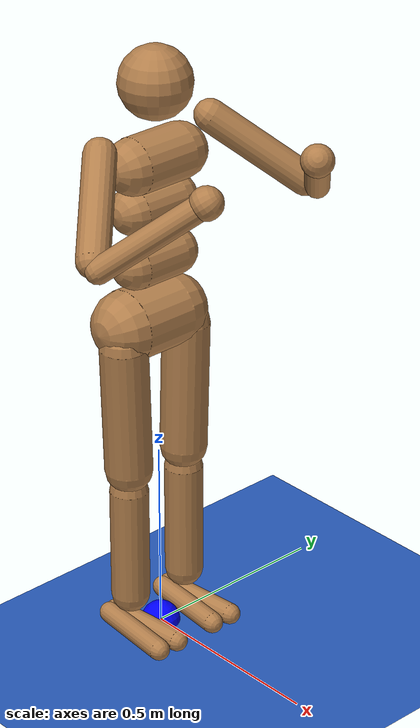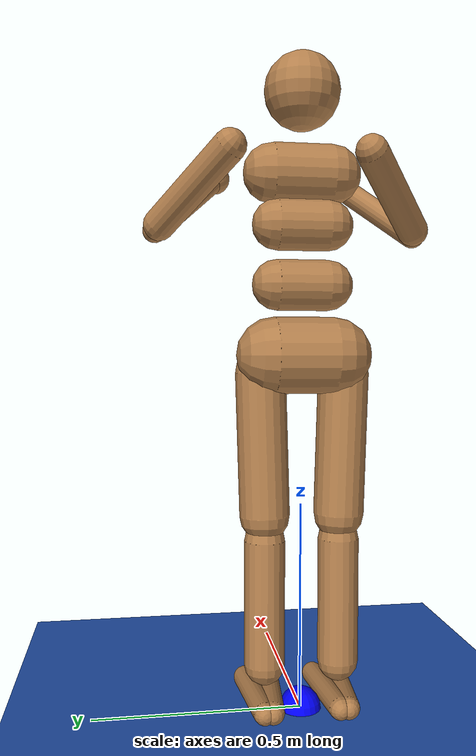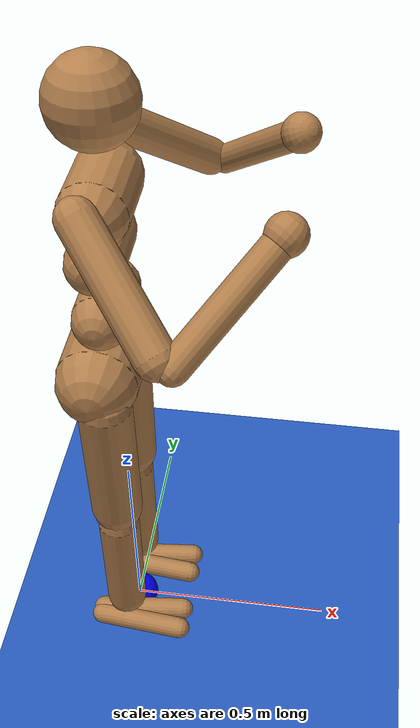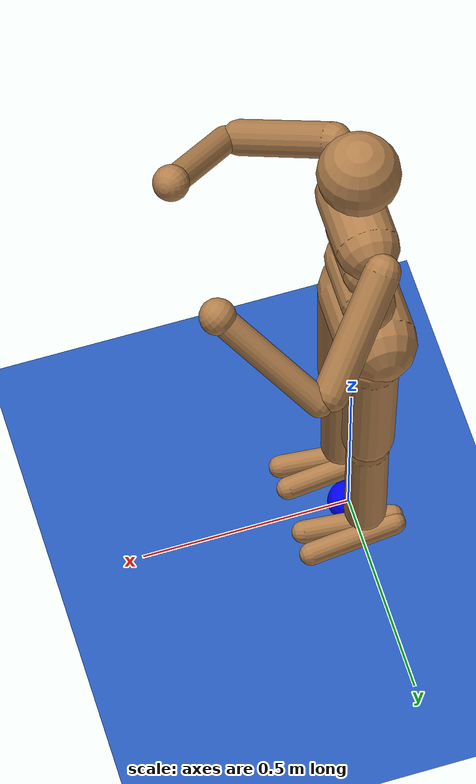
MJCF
<mujoco model="Humanoid Tracking">
  <include file="../../common.xml"/>
  <include file="../humanoid.xml" />
  <size memory="400K"/>

  <custom>
    <numeric name="task_transition" data="1" />
    <numeric name="sampling_representation" data="2" />
    <numeric name="agent_planner" data="2" />
    <numeric name="agent_horizon" data="0.5" />
    <numeric name="agent_timestep" data="0.004" />
    <numeric name="sampling_spline_points" data="16" />
    <numeric name="sampling_exploration" data="0.15" />
    <numeric name="sampling_trajectories" data="16" />
    <numeric name="gradient_spline_points" data="5" />
    <numeric name="ilqg_num_rollouts" data="6" />
    <numeric name="ilqg_regularization_type" data="1" />
    <numeric name="ilqg_representation" data="2" />
  </custom>

  <default>
    <default class="mocap_site">
      <site type="sphere" size="0.027" rgba="0 0 1 1" group="2" material="target"/>
    </default>
  </default>

  <worldbody>
    <body name="mocap[pelvis]" mocap="true">
      <site name="mocap[pelvis]" class="mocap_site" size="0.05" />
    </body>
    <body name="mocap[head]" mocap="true">
      <site name="mocap[head]" class="mocap_site" />
    </body>
    <body name="mocap[ltoe]" mocap="true">
      <site name="mocap[ltoe]" class="mocap_site" />
    </body>
    <body name="mocap[rtoe]" mocap="true">
      <site name="mocap[rtoe]" class="mocap_site" />
    </body>
    <body name="mocap[lheel]" mocap="true">
      <site name="mocap[lheel]" class="mocap_site" />
    </body>
    <body name="mocap[rheel]" mocap="true">
      <site name="mocap[rheel]" class="mocap_site" />
    </body>
    <body name="mocap[lknee]" mocap="true">
      <site name="mocap[lknee]" class="mocap_site" />
    </body>
    <body name="mocap[rknee]" mocap="true">
      <site name="mocap[rknee]" class="mocap_site" />
    </body>
    <body name="mocap[lhand]" mocap="true">
      <site name="mocap[lhand]" class="mocap_site" />
    </body>
    <body name="mocap[rhand]" mocap="true">
      <site name="mocap[rhand]" class="mocap_site" />
    </body>
    <body name="mocap[lelbow]" mocap="true">
      <site name="mocap[lelbow]" class="mocap_site" />
    </body>
    <body name="mocap[relbow]" mocap="true">
      <site name="mocap[relbow]" class="mocap_site" />
    </body>
    <body name="mocap[lshoulder]" mocap="true">
      <site name="mocap[lshoulder]" class="mocap_site" />
    </body>
    <body name="mocap[rshoulder]" mocap="true">
      <site name="mocap[rshoulder]" class="mocap_site" />
    </body>
    <body name="mocap[lhip]" mocap="true">
      <site name="mocap[lhip]" class="mocap_site" />
    </body>
    <body name="mocap[rhip]" mocap="true">
      <site name="mocap[rhip]" class="mocap_site" />
    </body>
  </worldbody>

  <sensor>
    <user name="control" dim="21" user="3 0 0.0 0.1 0.3" />
    <user name="joint vel." dim="27" user="0 0 0.0 0.1" />

    <user name="root pos error" dim="3" user="6 30.0 0.0 100.0 0.1" />
    <user name="head pos error" dim="3" user="6 30.0 0.0 100.0 0.1" />
    <user name="ltoe pos error" dim="3" user="6 30.0 0.0 100.0 0.1" />
    <user name="rtoe pos error" dim="3" user="6 30.0 0.0 100.0 0.1" />
    <user name="lheel pos error" dim="3" user="6 30.0 0.0 100.0 0.1" />
    <user name="rheel pos error" dim="3" user="6 30.0 0.0 100.0 0.1" />
    <user name="lknee pos error" dim="3" user="6 10.0 0.0 100.0 0.1" />
    <user name="rknee pos error" dim="3" user="6 10.0 0.0 100.0 0.1" />
    <user name="lhand pos error" dim="3" user="6 60.0 0.0 100.0 0.1" />
    <user name="rhand pos error" dim="3" user="6 60.0 0.0 100.0 0.1" />
    <user name="lelbow pos error" dim="3" user="6 10.0 0.0 100.0 0.1" />
    <user name="relbow pos error" dim="3" user="6 10.0 0.0 100.0 0.1" />
    <user name="lshoulder pos error" dim="3" user="6 30.0 0.0 100.0 0.1" />
    <user name="rshoulder pos error" dim="3" user="6 30.0 0.0 100.0 0.1" />
    <user name="lhip pos error" dim="3" user="6 30.0 0.0 100.0 0.1" />
    <user name="rhip pos error" dim="3" user="6 30.0 0.0 100.0 0.1" />

    <user name="root vel error" dim="3" user="6 0.003 0.0 1.0 0.1" />
    <user name="head vel error" dim="3" user="6 0.003 0.0 1.0 0.1" />
    <user name="ltoe vel error" dim="3" user="6 0.003 0.0 1.0 0.1" />
    <user name="rtoe vel error" dim="3" user="6 0.003 0.0 1.0 0.1" />
    <user name="lheel vel error" dim="3" user="6 0.003 0.0 1.0 0.1" />
    <user name="rheel vel error" dim="3" user="6 0.003 0.0 1.0 0.1" />
    <user name="lknee vel error" dim="3" user="6 0.003 0.0 1.0 0.1" />
    <user name="rknee vel error" dim="3" user="6 0.003 0.0 1.0 0.1" />
    <user name="lhand vel error" dim="3" user="6 0.003 0.0 1.0 0.1" />
    <user name="rhand vel error" dim="3" user="6 0.003 0.0 1.0 0.1" />
    <user name="lelbow vel error" dim="3" user="6 0.003 0.0 1.0 0.1" />
    <user name="relbow vel error" dim="3" user="6 0.003 0.0 1.0 0.1" />
    <user name="lshoulder vel error" dim="3" user="6 0.003 0.0 1.0 0.1" />
    <user name="rshoulder vel error" dim="3" user="6 0.003 0.0 1.0 0.1" />
    <user name="lhip vel error" dim="3" user="6 0.003 0.0 1.0 0.1" />
    <user name="rhip vel error" dim="3" user="6 0.003 0.0 1.0 0.1" />

    <framepos name="trace0" objtype="body" objname="torso"/>

    <framepos name="tracking_pos[pelvis]" objtype="site" objname="tracking[pelvis]" />
    <framepos name="tracking_pos[head]" objtype="site" objname="tracking[head]" />
    <framepos name="tracking_pos[ltoe]" objtype="site" objname="tracking[ltoe]" />
    <framepos name="tracking_pos[rtoe]" objtype="site" objname="tracking[rtoe]" />
    <framepos name="tracking_pos[lheel]" objtype="site" objname="tracking[lheel]" />
    <framepos name="tracking_pos[rheel]" objtype="site" objname="tracking[rheel]" />
    <framepos name="tracking_pos[lknee]" objtype="site" objname="tracking[lknee]" />
    <framepos name="tracking_pos[rknee]" objtype="site" objname="tracking[rknee]" />
    <framepos name="tracking_pos[lhand]" objtype="site" objname="tracking[lhand]" />
    <framepos name="tracking_pos[rhand]" objtype="site" objname="tracking[rhand]" />
    <framepos name="tracking_pos[lelbow]" objtype="site" objname="tracking[lelbow]" />
    <framepos name="tracking_pos[relbow]" objtype="site" objname="tracking[relbow]" />
    <framepos name="tracking_pos[lshoulder]" objtype="site" objname="tracking[lshoulder]" />
    <framepos name="tracking_pos[rshoulder]" objtype="site" objname="tracking[rshoulder]" />
    <framepos name="tracking_pos[lhip]" objtype="site" objname="tracking[lhip]" />
    <framepos name="tracking_pos[rhip]" objtype="site" objname="tracking[rhip]" />

    <framelinvel name="tracking_linvel[pelvis]" objtype="site" objname="tracking[pelvis]" />
    <framelinvel name="tracking_linvel[head]" objtype="site" objname="tracking[head]" />
    <framelinvel name="tracking_linvel[ltoe]" objtype="site" objname="tracking[ltoe]" />
    <framelinvel name="tracking_linvel[rtoe]" objtype="site" objname="tracking[rtoe]" />
    <framelinvel name="tracking_linvel[lheel]" objtype="site" objname="tracking[lheel]" />
    <framelinvel name="tracking_linvel[rheel]" objtype="site" objname="tracking[rheel]" />
    <framelinvel name="tracking_linvel[lknee]" objtype="site" objname="tracking[lknee]" />
    <framelinvel name="tracking_linvel[rknee]" objtype="site" objname="tracking[rknee]" />
    <framelinvel name="tracking_linvel[lhand]" objtype="site" objname="tracking[lhand]" />
    <framelinvel name="tracking_linvel[rhand]" objtype="site" objname="tracking[rhand]" />
    <framelinvel name="tracking_linvel[lelbow]" objtype="site" objname="tracking[lelbow]" />
    <framelinvel name="tracking_linvel[relbow]" objtype="site" objname="tracking[relbow]" />
    <framelinvel name="tracking_linvel[lshoulder]" objtype="site" objname="tracking[lshoulder]" />
    <framelinvel name="tracking_linvel[rshoulder]" objtype="site" objname="tracking[rshoulder]" />
    <framelinvel name="tracking_linvel[lhip]" objtype="site" objname="tracking[lhip]" />
    <framelinvel name="tracking_linvel[rhip]" objtype="site" objname="tracking[rhip]" />
  </sensor>

  <include file="./keyframes/CMU-CMU-02-02_04_poses.xml" />  <!-- simple jump, balance -->
</mujoco>

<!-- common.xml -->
<mujoco>

    <visual>
        <headlight ambient=".4 .4 .4" diffuse=".8 .8 .8" specular="0.1 0.1 0.1"/>
        <map znear=".01"/>
        <quality shadowsize="2048"/>
        <global elevation="-15"/>
    </visual>

    <asset>
        <texture name="blue_grid" type="2d" builtin="checker" rgb1=".02 .14 .44" rgb2=".27 .55 1" width="300" height="300" mark="edge" markrgb="1 1 1"/>
        <material name="blue_grid" texture="blue_grid" texrepeat="1 1" texuniform="true" reflectance=".2"/>

        <texture name="grey_grid" type="2d" builtin="checker" rgb1=".26 .26 .26" rgb2=".6 .6 .6" width="300" height="300" mark="edge" markrgb="1 1 1"/>
        <material name="grey_grid" texture="grey_grid" texrepeat="1 1" texuniform="true" reflectance=".2"/>
        <texture name="skybox" type="skybox" builtin="gradient" rgb1=".66 .79 1" rgb2=".9 .91 .93" width="800" height="800"/>

        <material name="self" rgba=".7 .5 .3 1"/>
        <material name="self_default" rgba=".7 .5 .3 1"/>
        <material name="self_highlight" rgba="0 .5 .3 1"/>
        <material name="effector" rgba=".7 .4 .2 1"/>
        <material name="effector_default" rgba=".7 .4 .2 1"/>
        <material name="effector_highlight" rgba="0 .5 .3 1"/>
        <material name="decoration" rgba=".2 .6 .3 1"/>
        <material name="eye" rgba="0 .2 1 1"/>
        <material name="target" rgba=".6 .3 .3 1"/>
        <material name="target_default" rgba=".6 .3 .3 1"/>
        <material name="target_highlight" rgba=".6 .3 .3 .4"/>
        <material name="site" rgba=".5 .5 .5 .3"/>
    </asset>

    <size memory="1M"/>

    <statistic extent="0.4" center="0.3 0.1 0"/>

    <visual>
        <quality shadowsize="8192"/>
        <global azimuth="180" elevation="-30"/>
    </visual>

    <default>
        <geom friction="1.0"/>
    </default>

    <compiler angle="radian" autolimits="true"/>

    <asset>
        <mesh name="apple" file="../../shared_assets/apple/apple.obj" />
        <mesh name="apple_contact0" file="../../shared_assets/apple/contact0.stl"  />
        <mesh name="apple_contact1" file="../../shared_assets/apple/contact1.stl"  />

        <mesh name="doorknob" file="../../shared_assets/doorknob/doorknob.obj" />

        <mesh name="flashlight" file="../../shared_assets/flashlight/flashlight.obj" />
        <mesh name="flashlight_contact0" file="../../shared_assets/flashlight/contact0.stl"  />
        <mesh name="flashlight_contact1" file="../../shared_assets/flashlight/contact1.stl"  />

        <mesh name="hammer" file="../../shared_assets/hammer/hammer.obj" />
        <mesh name="hammer_contact0" file="../../shared_assets/hammer/contact0.stl"  />
        <mesh name="hammer_contact1" file="../../shared_assets/hammer/contact1.stl"  />

        <mesh name="phone" file="../../shared_assets/phone/phone.obj" />
        <mesh name="phone_contact0" file="../../shared_assets/phone/contact0.stl"  />
        <mesh name="phone_contact1" file="../../shared_assets/phone/contact1.stl"  />
        <mesh name="phone_contact2" file="../../shared_assets/phone/contact2.stl"  />

        <mesh name="stapler" file="../../shared_assets/stapler/stapler.obj" />
        <mesh name="stapler_contact0" file="../../shared_assets/stapler/contact0.stl"  />
        <mesh name="stapler_contact1" file="../../shared_assets/stapler/contact1.stl"  />
        <mesh name="stapler_contact2" file="../../shared_assets/stapler/contact2.stl"  />
        <mesh name="stapler_contact3" file="../../shared_assets/stapler/contact3.stl"  />
        <mesh name="stapler_contact4" file="../../shared_assets/stapler/contact4.stl"  />

        <mesh name="waterbottle" file="../../shared_assets/waterbottle/waterbottle.obj" />
        <mesh name="waterbottle_contact0" file="../../shared_assets/waterbottle/contact0.stl"  />
        <mesh name="waterbottle_contact1" file="../../shared_assets/waterbottle/contact1.stl"  />
    </asset>

</mujoco>

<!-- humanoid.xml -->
<mujoco model="Humanoid">

  <statistic extent="2" center="0 0 1"/>

  <default>
    <motor ctrlrange="-1 1" ctrllimited="true"/>
    <site size=".04" group="3"/>
    <default class="body">

      <!-- geoms -->
      <geom type="capsule" condim="1" friction=".7" solimp=".9 .99 .003" solref=".015 1" material="self"/>
      <default class="thigh">
        <geom size=".06"/>
      </default>
      <default class="shin">
        <geom fromto="0 0 0 0 0 -.3"  size=".049"/>
      </default>
      <default class="foot">
        <geom size=".027"/>
        <default class="foot1">
          <geom fromto="-.07 -.01 0 .14 -.03 0"/>
        </default>
        <default class="foot2">
          <geom fromto="-.07 .01 0 .14  .03 0"/>
        </default>
      </default>
      <default class="arm_upper">
        <geom size=".04"/>
      </default>
      <default class="arm_lower">
        <geom size=".031"/>
      </default>
      <default class="hand">
        <geom type="sphere" size=".04"/>
      </default>

      <!-- joints -->
      <joint type="hinge" damping=".2" stiffness="1" armature=".01" limited="true" solimplimit="0 .99 .01"/>
      <default class="joint_big">
        <joint damping="5" stiffness="10"/>
        <default class="hip_x">
          <joint range="-30 10"/>
        </default>
        <default class="hip_z">
          <joint range="-60 35"/>
        </default>
        <default class="hip_y">
          <joint axis="0 1 0" range="-150 20"/>
        </default>
        <default class="joint_big_stiff">
          <joint stiffness="20"/>
        </default>
      </default>
      <default class="knee">
        <joint pos="0 0 .02" axis="0 -1 0" range="-160 2"/>
      </default>
      <default class="ankle">
        <joint range="-50 50"/>
        <default class="ankle_y">
          <joint pos="0 0 .08" axis="0 1 0" stiffness="6"/>
        </default>
        <default class="ankle_x">
          <joint pos="0 0 .04" stiffness="3"/>
        </default>
      </default>
      <default class="shoulder">
        <joint range="-85 60"/>
      </default>
      <default class="elbow">
        <joint range="-100 50" stiffness="0"/>
      </default>

      <!-- tracking site -->
      <default class="tracking_site">
        <site type="sphere" size="0.027" rgba="1 0 0 1" group="3"/>
      </default>
    </default>
  </default>

  <worldbody>
    <geom name="floor" type="plane" conaffinity="1" size="50 50 .05" material="blue_grid"/>
    <body name="torso" pos="0 0 1.282" childclass="body">
      <light name="top" pos="0 0 2" mode="trackcom"/>
      <camera name="back" pos="-3 0 1" xyaxes="0 -1 0 1 0 2" mode="trackcom"/>
      <camera name="side" pos="0 -3 1" xyaxes="1 0 0 0 1 2" mode="trackcom"/>
      <freejoint name="root"/>
      <geom name="torso" fromto="0 -.07 0 0 .07 0" size=".07"/>
      <geom name="waist_upper" fromto="-.01 -.06 -.12 -.01 .06 -.12" size=".06"/>
      <body name="head" pos="0 0 .19">
        <geom name="head" type="sphere" size=".09"/>
        <site name="tracking[head]" class="tracking_site" pos="0.09 0 0" />
        <camera name="egocentric" pos=".09 0 0" xyaxes="0 -1 0 .1 0 1" fovy="80"/>
      </body>
      <body name="waist_lower" pos="-.01 0 -.26">
        <geom name="waist_lower" fromto="0 -.06 0 0 .06 0" size=".06"/>
        <joint name="abdomen_z" pos="0 0 .065" axis="0 0 1" range="-45 45" class="joint_big_stiff"/>
        <joint name="abdomen_y" pos="0 0 .065" axis="0 1 0" range="-75 30" class="joint_big"/>
        <body name="pelvis" pos="0 0 -.165">
          <site name="tracking[pelvis]" class="tracking_site" pos="0 0 0.075" size=".05" />
          <joint name="abdomen_x" pos="0 0 .1" axis="1 0 0" range="-35 35" class="joint_big"/>
          <geom name="butt" fromto="-.02 -.07 0 -.02 .07 0" size=".09"/>
          <body name="thigh_right" pos="0 -.1 -.04">
            <site name="tracking[rhip]" class="tracking_site" pos="0 0.025 0.025" />
            <joint name="hip_x_right" axis="1 0 0" class="hip_x"/>
            <joint name="hip_z_right" axis="0 0 1" class="hip_z"/>
            <joint name="hip_y_right" class="hip_y"/>
            <geom name="thigh_right" fromto="0 0 0 0 .01 -.34" class="thigh"/>
            <body name="shin_right" pos="0 .01 -.4">
              <joint name="knee_right" class="knee"/>
              <site name="tracking[rknee]" class="tracking_site" pos="0 0 0.05" />
              <geom name="shin_right" class="shin"/>
              <body name="foot_right" pos="0 0 -.39">
                <joint name="ankle_y_right" class="ankle_y"/>
                <joint name="ankle_x_right" class="ankle_x" axis="1 0 .5"/>
                <geom name="foot1_right" class="foot1"/>
                <geom name="foot2_right" class="foot2"/>
                <site name="foot_right" pos=".05 .03 0" type="sphere" size=".027"/>
                <site name="sp2" pos="-.07 0 0" type="sphere" size=".027"/>
                <site name="sp3" pos=".14 0 0" type="sphere" size=".027"/>
                <body name="heel_right" pos="-0.05 0 0.04">
                  <site name="tracking[rheel]" class="tracking_site" />
                </body>
                <body name="toe_right" pos="0.07 0 -0.01">
                  <site name="tracking[rtoe]" class="tracking_site" />
                </body>
              </body>
            </body>
          </body>
          <body name="thigh_left" pos="0 .1 -.04">
            <site name="tracking[lhip]" class="tracking_site" pos="0 -0.025 0.025" />
            <joint name="hip_x_left" axis="-1 0 0" class="hip_x"/>
            <joint name="hip_z_left" axis="0 0 -1" class="hip_z"/>
            <joint name="hip_y_left" class="hip_y"/>
            <geom name="thigh_left" fromto="0 0 0 0 -.01 -.34" class="thigh"/>
            <body name="shin_left" pos="0 -.01 -.4">
              <joint name="knee_left" class="knee"/>
              <site name="tracking[lknee]" class="tracking_site" pos="0 0 0.05" />
              <geom name="shin_left" fromto="0 0 0 0 0 -.3" class="shin"/>
              <body name="foot_left" pos="0 0 -.39">
                <joint name="ankle_y_left" class="ankle_y"/>
                <joint name="ankle_x_left" class="ankle_x" axis="-1 0 -.5"/>
                <geom name="foot1_left" class="foot1"/>
                <geom name="foot2_left" class="foot2"/>
                <site name="foot_left" pos=".05 0 0" type="sphere" size=".027"/>
                <site name="sp0" pos="-.07 0 0" type="sphere" size=".027"/>
                <site name="sp1" pos=".14 0 0" type="sphere" size=".027"/>
                <body name="heel_left" pos="-0.05 0 0.04">
                  <site name="tracking[lheel]" class="tracking_site" />
                </body>
                <body name="toe_left" pos="0.07 0 -0.01">
                  <site name="tracking[ltoe]" class="tracking_site" />
                </body>
              </body>
            </body>
          </body>
        </body>
      </body>
      <body name="upper_arm_right" pos="0 -.17 .06">
        <site name="tracking[rshoulder]" class="tracking_site" />
        <joint name="shoulder1_right" axis="2 1 1"  class="shoulder"/>
        <joint name="shoulder2_right" axis="0 -1 1" class="shoulder"/>
        <geom name="upper_arm_right" fromto="0 0 0 .16 -.16 -.16" class="arm_upper"/>
        <body name="lower_arm_right" pos=".18 -.18 -.18">
          <joint name="elbow_right" axis="0 -1 1" class="elbow"/>
          <site name="tracking[relbow]" class="tracking_site" />
          <site name="tracking[rhand]" class="tracking_site" pos="0.13 0.13 0.13" />
          <geom name="lower_arm_right" fromto=".01 .01 .01 .17 .17 .17" class="arm_lower"/>
          <body name="hand_right" pos=".18 .18 .18">
            <geom name="hand_right" zaxis="1 1 1" class="hand"/>
          </body>
        </body>
      </body>
      <body name="upper_arm_left" pos="0 .17 .06">
        <site name="tracking[lshoulder]" class="tracking_site" />
        <joint name="shoulder1_left" axis="-2 1 -1" class="shoulder"/>
        <joint name="shoulder2_left" axis="0 -1 -1"  class="shoulder"/>
        <geom name="upper_arm_left" fromto="0 0 0 .16 .16 -.16" class="arm_upper"/>
        <body name="lower_arm_left" pos=".18 .18 -.18">
          <joint name="elbow_left" axis="0 -1 -1" class="elbow"/>
          <site name="tracking[lelbow]" class="tracking_site" />
          <site name="tracking[lhand]" class="tracking_site" pos="0.13 -0.13 0.13" />
          <geom name="lower_arm_left" fromto=".01 -.01 .01 .17 -.17 .17" class="arm_lower"/>
          <body name="hand_left" pos=".18 -.18 .18">
            <geom name="hand_left" zaxis="1 -1 1" class="hand"/>
          </body>
        </body>
      </body>
    </body>
  </worldbody>

  <contact>
    <exclude body1="waist_lower" body2="thigh_right"/>
    <exclude body1="waist_lower" body2="thigh_left"/>
  </contact>

  <tendon>
    <fixed name="hamstring_right" limited="true" range="-0.3 2">
      <joint joint="hip_y_right" coef=".5"/>
      <joint joint="knee_right" coef="-.5"/>
    </fixed>
    <fixed name="hamstring_left" limited="true" range="-0.3 2">
      <joint joint="hip_y_left" coef=".5"/>
      <joint joint="knee_left" coef="-.5"/>
    </fixed>
  </tendon>

  <actuator>
    <motor name="abdomen_y"       gear="40"  joint="abdomen_y"/>
    <motor name="abdomen_z"       gear="40"  joint="abdomen_z"/>
    <motor name="abdomen_x"       gear="40"  joint="abdomen_x"/>
    <motor name="hip_x_right"     gear="40"  joint="hip_x_right"/>
    <motor name="hip_z_right"     gear="40"  joint="hip_z_right"/>
    <motor name="hip_y_right"     gear="120" joint="hip_y_right"/>
    <motor name="knee_right"      gear="100" joint="knee_right"/>
    <motor name="ankle_x_right"   gear="20"  joint="ankle_x_right"/>
    <motor name="ankle_y_right"   gear="20"  joint="ankle_y_right"/>
    <motor name="hip_x_left"      gear="40"  joint="hip_x_left"/>
    <motor name="hip_z_left"      gear="40"  joint="hip_z_left"/>
    <motor name="hip_y_left"      gear="120" joint="hip_y_left"/>
    <motor name="knee_left"       gear="100" joint="knee_left"/>
    <motor name="ankle_x_left"    gear="20"  joint="ankle_x_left"/>
    <motor name="ankle_y_left"    gear="20"  joint="ankle_y_left"/>
    <motor name="shoulder1_right" gear="20"  joint="shoulder1_right"/>
    <motor name="shoulder2_right" gear="20"  joint="shoulder2_right"/>
    <motor name="elbow_right"     gear="40"  joint="elbow_right"/>
    <motor name="shoulder1_left"  gear="20"  joint="shoulder1_left"/>
    <motor name="shoulder2_left"  gear="20"  joint="shoulder2_left"/>
    <motor name="elbow_left"      gear="40"  joint="elbow_left"/>
  </actuator>

</mujoco>

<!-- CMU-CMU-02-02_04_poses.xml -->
<mujoco>
  <keyframe>
    <key name="home" mpos="0.0 0.0 0.9079 0.02246 -0.01716 1.48528 0.05642 0.11259 0.02555 0.05707 -0.10348 0.01632 -0.06685 0.06839 0.05535 -0.06679 -0.06662 0.05473 0.03258 0.09748 0.4423 0.05061 -0.09743 0.43688 0.07061 0.19745 0.86066 0.02813 -0.23827 0.85899 -0.07446 0.17572 1.06235 -0.11842 -0.18084 1.06022 -0.02793 0.17321 1.31954 -0.07074 -0.17717 1.31069 0.00543 0.07048 0.81714 -0.00302 -0.06647 0.81644" qpos="0.0 0.0 0.9079 0.47729 0.4768 0.51538 0.52843 -0.37764 0.12913 0.0425 0.23666 0.12376 -0.46211 0.0 0.34624 -0.2247 0.03961 0.28685 -0.14095 -0.42425 0.0 -0.01328 -0.06323 -0.13403 -0.0012 -0.06067 -0.05299 -0.0022 -0.06082 0.03187 0.00511 -0.001 0.07284 0.00468 -0.00359 0.00608 -0.00042 -0.00288 -0.10694 0.0 -0.06804 1.23638 0.29711 -0.77432 0.58544 0.0 0.0 0.0 0.7854 0.0 0.785 0.0 0.01397 -1.1 -0.23616 -0.74477 0.61064 0.0 0.0 0.0 0.7854 0.0 0.785" qvel="-0.08354 0.02754 0.01539 0.16814 0.16441 0.10931 -0.21087 -0.00294 -0.264 -0.01938 0.00421 -0.04574 0.0 -0.12916 -0.16328 -0.27899 -0.00141 0.04089 -0.1313 0.0 -0.25084 -0.01123 0.39602 -0.08658 0.04064 -0.03659 0.14236 0.04549 -0.48126 0.12148 -0.06003 0.49372 0.07806 -0.05437 0.26152 0.0054 -0.0533 -0.09482 0.0 -0.99097 1.348 0.37312 0.58397 1.16959 0.0 0.0 0.0 0.0 0.0 0.0 0.0 1.1114 0.0 -1.09838 -0.35403 1.03716 0.0 0.0 0.0 0.0 0.0 0.0" />
    <key mpos="-0.00278 0.00092 0.90841 0.03145 -0.01514 1.48526 0.05536 0.1125 0.026 0.05724 -0.10392 0.01725 -0.06788 0.06821 0.05577 -0.06686 -0.06709 0.05491 0.0304 0.09733 0.44302 0.04967 -0.09601 0.43748 0.09347 0.18599 0.87476 0.04656 -0.23019 0.87018 -0.06943 0.17917 1.06348 -0.11361 -0.1823 1.06336 -0.02236 0.17345 1.32052 -0.06289 -0.17806 1.31322 0.00172 0.0717 0.81784 -0.00597 -0.06529 0.81677" />
    <key mpos="-0.00899 0.00158 0.90934 0.04263 -0.01308 1.48478 0.05386 0.11235 0.02793 0.05651 -0.10436 0.01844 -0.06942 0.06778 0.05713 -0.06721 -0.06679 0.0566 0.02813 0.09732 0.44453 0.0493 -0.09444 0.43926 0.11315 0.17586 0.89001 0.06421 -0.22192 0.88196 -0.06414 0.183 1.06527 -0.10809 -0.1846 1.06687 -0.01604 0.17373 1.32201 -0.05384 -0.17884 1.31596 -0.0062 0.07268 0.81894 -0.01323 -0.06435 0.81753" />
    <key mpos="-0.01506 0.00222 0.91052 0.0561 -0.01127 1.48376 0.05279 0.11203 0.02971 0.05648 -0.10463 0.02086 -0.07066 0.06773 0.0586 -0.06707 -0.06593 0.05847 0.02583 0.09767 0.44624 0.04844 -0.09314 0.44148 0.12755 0.16944 0.9073 0.07703 -0.21552 0.89107 -0.06147 0.19067 1.06862 -0.1021 -0.18884 1.07126 -0.00779 0.17432 1.3239 -0.04326 -0.17922 1.31919 -0.01344 0.07344 0.82019 -0.02036 -0.0636 0.8187" />
    <key mpos="-0.02271 0.00298 0.91122 0.07551 -0.00926 1.4797 0.0518 0.11182 0.03081 0.05825 -0.10374 0.02341 -0.07165 0.0677 0.05997 -0.06537 -0.06502 0.06076 0.02375 0.09696 0.44792 0.04908 -0.09093 0.44417 0.13236 0.16972 0.92107 0.08031 -0.21406 0.89278 -0.06114 0.20346 1.07476 -0.09575 -0.19622 1.07704 0.00274 0.17481 1.32658 -0.03147 -0.17899 1.32319 -0.0234 0.07444 0.82107 -0.0304 -0.06258 0.81938" />
    <key mpos="-0.03 0.00446 0.91201 0.09562 -0.00742 1.47363 0.05037 0.11175 0.03292 0.05827 -0.10331 0.02698 -0.07305 0.06773 0.06238 -0.06504 -0.06355 0.06424 0.02399 0.09605 0.45 0.05054 -0.08845 0.44738 0.1252 0.18174 0.92066 0.07035 -0.22038 0.88563 -0.06125 0.21672 1.08257 -0.09129 -0.20561 1.08291 0.01594 0.17587 1.32892 -0.01622 -0.17862 1.3251 -0.03227 0.0761 0.82203 -0.03966 -0.0609 0.82022" />
    <key mpos="-0.03782 0.00588 0.91082 0.1193 -0.00616 1.46243 0.04852 0.11164 0.03384 0.05894 -0.1024 0.0292 -0.07478 0.06744 0.06352 -0.06426 -0.06204 0.06619 0.02424 0.09601 0.45062 0.0523 -0.0857 0.44911 0.10254 0.20825 0.90719 0.04563 -0.23497 0.87215 -0.0652 0.23161 1.09026 -0.09081 -0.2181 1.08749 0.03137 0.17606 1.3267 0.00277 -0.17914 1.32147 -0.04233 0.07765 0.82103 -0.04912 -0.05938 0.81914" />
    <key mpos="-0.04575 0.00793 0.90738 0.14685 -0.00499 1.44472 0.04578 0.11263 0.03428 0.059 -0.10104 0.03009 -0.07728 0.06821 0.0646 -0.06372 -0.05984 0.06774 0.02746 0.09818 0.45009 0.05636 -0.08292 0.44961 0.06414 0.24878 0.88912 0.00679 -0.25792 0.85815 -0.07249 0.24791 1.09776 -0.09419 -0.23067 1.09124 0.04876 0.17629 1.31796 0.02296 -0.17917 1.3118 -0.05228 0.07993 0.81789 -0.05845 -0.05713 0.81574" />
    <key mpos="-0.05378 0.0098 0.89965 0.17729 -0.00405 1.41828 0.04485 0.11409 0.03268 0.06012 -0.10057 0.03041 -0.07757 0.06873 0.06419 -0.06232 -0.05856 0.06809 0.03499 0.10116 0.44726 0.065 -0.07983 0.4477 0.00796 0.29719 0.87658 -0.04621 -0.28605 0.84891 -0.08317 0.26206 1.10606 -0.10159 -0.24133 1.09427 0.06727 0.17632 1.30184 0.04248 -0.17858 1.29508 -0.06343 0.08181 0.81045 -0.06689 -0.05535 0.80813" />
    <key mpos="-0.06161 0.01096 0.88659 0.20762 -0.00289 1.38251 0.0434 0.11624 0.03018 0.06268 -0.09938 0.02897 -0.07853 0.07009 0.06242 -0.05935 -0.05695 0.06749 0.04606 0.10523 0.44152 0.07824 -0.07649 0.4436 -0.0616 0.34414 0.87945 -0.10889 -0.31311 0.85085 -0.09488 0.27422 1.11652 -0.11173 -0.249 1.09814 0.08668 0.17657 1.2772 0.06146 -0.1776 1.27114 -0.07411 0.08322 0.79795 -0.07614 -0.05395 0.79512" />
    <key mpos="-0.06869 0.0118 0.86774 0.23778 -0.00148 1.3365 0.04377 0.1183 0.0265 0.06483 -0.09818 0.0268 -0.0776 0.07126 0.05958 -0.057 -0.05541 0.0656 0.06294 0.10772 0.43292 0.09415 -0.07317 0.43656 -0.13261 0.38163 0.90052 -0.17287 -0.33532 0.86643 -0.10193 0.28195 1.12706 -0.1195 -0.2524 1.10211 0.10723 0.177 1.24347 0.0814 -0.17604 1.23933 -0.08323 0.08404 0.77939 -0.08456 -0.05314 0.77651" />
    <key mpos="-0.0746 0.01291 0.84172 0.26503 -0.00011 1.28045 0.04626 0.12074 0.02272 0.06714 -0.0981 0.02211 -0.07455 0.07233 0.05588 -0.05427 -0.05442 0.06121 0.08499 0.11057 0.42133 0.11261 -0.07069 0.42543 -0.19586 0.40393 0.93723 -0.22995 -0.3479 0.89488 -0.10527 0.28045 1.13407 -0.12314 -0.25063 1.10559 0.1252 0.17748 1.20187 0.1008 -0.1746 1.20093 -0.09108 0.08482 0.75345 -0.09143 -0.05237 0.75091" />
    <key mpos="-0.07955 0.01393 0.80897 0.29052 0.0007 1.21617 0.05008 0.1228 0.01857 0.07127 -0.09891 0.01773 -0.07052 0.07347 0.05109 -0.04991 -0.05474 0.05698 0.10905 0.11067 0.40724 0.13437 -0.06906 0.41281 -0.24421 0.40662 0.98384 -0.27549 -0.34821 0.93062 -0.10043 0.27119 1.13611 -0.12095 -0.24398 1.10532 0.14281 0.17693 1.15241 0.11924 -0.17334 1.15371 -0.0982 0.08556 0.7209 -0.09809 -0.05164 0.71869" />
    <key mpos="-0.08395 0.01483 0.76988 0.31131 0.00258 1.1446 0.05496 0.12539 0.01402 0.07564 -0.09911 0.01196 -0.06503 0.07479 0.04688 -0.04455 -0.05382 0.05295 0.13461 0.11053 0.39232 0.15842 -0.06704 0.39849 -0.27489 0.3908 1.02848 -0.3033 -0.33874 0.96759 -0.09045 0.25728 1.13022 -0.11122 -0.23431 1.09977 0.156 0.17693 1.09672 0.13597 -0.17173 1.09995 -0.10462 0.08667 0.68244 -0.10345 -0.05051 0.67965" />
    <key mpos="-0.08654 0.01625 0.72745 0.32795 0.00386 1.07359 0.06272 0.12813 0.01065 0.08061 -0.10033 0.00763 -0.0569 0.07648 0.0432 -0.03897 -0.05461 0.04989 0.15981 0.11069 0.37836 0.18226 -0.06604 0.3841 -0.28329 0.36316 1.05832 -0.31416 -0.32008 0.99536 -0.07321 0.24017 1.11253 -0.09616 -0.2213 1.08474 0.16908 0.17598 1.03842 0.1507 -0.17095 1.04546 -0.10908 0.08923 0.64143 -0.10723 -0.04788 0.63662" />
    <key mpos="-0.08599 0.01887 0.68682 0.3409 0.00466 1.00744 0.06939 0.13122 0.0078 0.08492 -0.10165 0.00338 -0.04963 0.07822 0.0404 -0.03354 -0.05554 0.04832 0.18259 0.11173 0.36509 0.20621 -0.06351 0.36962 -0.27557 0.33145 1.06178 -0.30954 -0.30021 1.00432 -0.05606 0.21468 1.08113 -0.07783 -0.20562 1.05557 0.18085 0.17656 0.97749 0.1658 -0.17174 0.98834 -0.10979 0.09286 0.602 -0.10496 -0.04408 0.59479" />
    <key mpos="-0.0836 0.02144 0.65138 0.35308 0.00488 0.95179 0.07485 0.1332 0.00706 0.08995 -0.10158 0.00227 -0.04393 0.07999 0.04015 -0.02749 -0.05498 0.04932 0.20163 0.11407 0.3548 0.227 -0.05764 0.35916 -0.26745 0.29723 1.03209 -0.30336 -0.27739 0.98825 -0.04114 0.19322 1.04503 -0.06558 -0.18862 1.01744 0.19266 0.17588 0.92949 0.17653 -0.17234 0.9391 -0.1087 0.09636 0.56776 -0.10152 -0.04035 0.55836" />
    <key mpos="-0.07796 0.02187 0.62646 0.36398 0.00432 0.91358 0.07877 0.13287 0.0078 0.09055 -0.10189 0.00145 -0.03958 0.07923 0.04178 -0.02666 -0.0542 0.04795 0.21794 0.1149 0.34655 0.24077 -0.0521 0.3467 -0.26534 0.2753 0.97435 -0.30281 -0.26075 0.94353 -0.03685 0.17922 1.00196 -0.06178 -0.18039 0.97029 0.20037 0.17633 0.89227 0.18354 -0.1739 0.90104 -0.10318 0.09672 0.54281 -0.09527 -0.03994 0.53333" />
    <key mpos="-0.06888 0.02195 0.61515 0.37309 0.00347 0.89772 0.08039 0.13178 0.00917 0.09108 -0.10216 0.00088 -0.03771 0.07754 0.04305 -0.02603 -0.05194 0.04492 0.23008 0.11401 0.33873 0.25114 -0.04747 0.33463 -0.2685 0.26922 0.8872 -0.30499 -0.24976 0.8691 -0.0447 0.18149 0.95364 -0.06489 -0.17787 0.91861 0.20281 0.17668 0.86979 0.18629 -0.1769 0.87472 -0.09312 0.09734 0.5317 -0.08495 -0.03925 0.52139" />
    <key mpos="-0.05825 0.01935 0.61698 0.37939 0.00378 0.90787 0.08042 0.12974 0.01042 0.09096 -0.10256 5e-05 -0.03694 0.07555 0.04686 -0.02544 -0.05088 0.04428 0.23845 0.11252 0.33541 0.25859 -0.0409 0.32713 -0.26156 0.27381 0.77411 -0.29647 -0.24285 0.766 -0.05593 0.1988 0.89365 -0.06762 -0.18129 0.86143 0.2027 0.17689 0.86292 0.18735 -0.17805 0.86275 -0.08184 0.09439 0.53303 -0.07232 -0.04214 0.5231" />
    <key mpos="-0.04701 0.01818 0.63147 0.37913 0.00637 0.94369 0.07848 0.12842 0.01123 0.08985 -0.10331 0.0 -0.03818 0.07428 0.0499 -0.02618 -0.05353 0.04727 0.24182 0.10984 0.33416 0.26227 -0.03562 0.3252 -0.20781 0.28209 0.64346 -0.2468 -0.23694 0.64207 -0.04945 0.21297 0.82331 -0.05538 -0.17994 0.80137 0.20344 0.17845 0.87961 0.18906 -0.17539 0.87379 -0.06894 0.09261 0.54653 -0.05824 -0.0439 0.5376" />
    <key mpos="-0.03841 0.01623 0.65443 0.36636 0.00967 1.0021 0.07615 0.1255 0.01315 0.08942 -0.10399 0.00228 -0.03976 0.07173 0.0545 -0.02634 -0.05547 0.0515 0.24056 0.10796 0.33836 0.26132 -0.03545 0.33012 -0.06604 0.28286 0.5454 -0.12167 -0.22814 0.5339 -0.01448 0.23332 0.78433 -0.01749 -0.17859 0.76185 0.2028 0.18202 0.92024 0.18877 -0.17304 0.91167 -0.05723 0.09042 0.56855 -0.04649 -0.04613 0.56042" />
    <key mpos="-0.03179 0.0146 0.68429 0.34147 0.01401 1.07516 0.07295 0.12203 0.01402 0.08806 -0.10383 0.00724 -0.04264 0.06867 0.05678 -0.02726 -0.056 0.05814 0.23266 0.10645 0.34531 0.25577 -0.0408 0.34176 0.13481 0.27889 0.54102 0.0691 -0.21466 0.50326 0.05227 0.27182 0.77625 0.03846 -0.18033 0.75455 0.202 0.18594 0.97251 0.18384 -0.16952 0.96376 -0.04731 0.08763 0.59677 -0.03703 -0.04907 0.59097" />
    <key mpos="-0.02408 0.01408 0.72102 0.31066 0.01963 1.1552 0.06952 0.1194 0.0151 0.08719 -0.10083 0.01397 -0.04515 0.06594 0.06015 -0.02705 -0.05529 0.0692 0.22107 0.10578 0.35681 0.24816 -0.04991 0.36076 0.32491 0.27093 0.64694 0.26715 -0.19497 0.58761 0.14673 0.30982 0.81706 0.10757 -0.19012 0.78705 0.20205 0.18941 1.04235 0.18104 -0.16392 1.02982 -0.03602 0.08534 0.63151 -0.02744 -0.05158 0.62899" />
    <key mpos="-0.01327 0.01681 0.76832 0.28073 0.02746 1.23811 0.06509 0.11818 0.01888 0.08687 -0.09784 0.02257 -0.04787 0.06505 0.06842 -0.0255 -0.05362 0.0825 0.2041 0.10553 0.37719 0.23555 -0.06194 0.38674 0.4489 0.26208 0.82921 0.40369 -0.1735 0.76408 0.23064 0.34167 0.9199 0.17098 -0.20114 0.86582 0.19729 0.1917 1.13136 0.17853 -0.15497 1.11649 -0.02325 0.08611 0.67703 -0.01564 -0.05089 0.67775" />
    <key mpos="0.0035 0.02176 0.83202 0.25564 0.03462 1.33025 0.06031 0.11661 0.02921 0.08471 -0.09337 0.03235 -0.05093 0.06501 0.084 -0.0244 -0.05251 0.1002 0.1782 0.10715 0.40987 0.21223 -0.0758 0.42306 0.49829 0.25705 1.02051 0.46205 -0.1534 0.96242 0.27539 0.36216 1.05878 0.2143 -0.21279 0.98145 0.1857 0.19189 1.23564 0.17241 -0.1429 1.22307 -0.00353 0.08974 0.73948 0.00011 -0.0474 0.74259" />
    <key mpos="0.02709 0.02873 0.91315 0.23109 0.04058 1.43943 0.05281 0.11315 0.04391 0.07864 -0.08956 0.04401 -0.05357 0.06732 0.11188 -0.02421 -0.05525 0.12414 0.13539 0.11415 0.46198 0.16927 -0.09225 0.47339 0.49857 0.25724 1.17247 0.46835 -0.13481 1.13316 0.27339 0.36348 1.18684 0.22706 -0.21523 1.10906 0.16493 0.19307 1.3527 0.15626 -0.13408 1.34019 0.02092 0.0967 0.82054 0.0199 -0.04047 0.82397" />
    <key mpos="0.05601 0.03309 1.00637 0.20801 0.04376 1.55517 0.05136 0.11093 0.06222 0.07101 -0.08962 0.0547 -0.03563 0.07594 0.15837 -0.01105 -0.06827 0.15951 0.07694 0.12574 0.53957 0.10056 -0.10417 0.54295 0.47947 0.25387 1.27734 0.45042 -0.11824 1.25976 0.24873 0.34842 1.2814 0.21374 -0.20658 1.2217 0.14212 0.19686 1.46573 0.13726 -0.13291 1.45353 0.04793 0.10184 0.91448 0.04408 -0.0353 0.91708" />
    <key mpos="0.08304 0.03234 1.09016 0.18391 0.0419 1.65081 0.05556 0.13225 0.12632 0.05168 -0.1214 0.12833 -0.01512 0.08597 0.23072 -0.01547 -0.06789 0.23227 0.03757 0.13116 0.62524 0.0586 -0.11096 0.62397 0.45104 0.24634 1.34075 0.42663 -0.10488 1.34908 0.21677 0.33117 1.35188 0.19203 -0.19958 1.31356 0.12298 0.19836 1.55653 0.11591 -0.13492 1.54818 0.06954 0.10189 0.99953 0.06688 -0.03529 1.00095" />
    <key mpos="0.09726 0.03239 1.1625 0.16366 0.04121 1.7313 -0.00805 0.13226 0.2045 -0.02808 -0.124 0.21276 -0.05636 0.07928 0.31806 -0.06791 -0.05524 0.32167 0.05526 0.13805 0.69826 0.06188 -0.11118 0.6969 0.42114 0.24005 1.37621 0.40484 -0.09328 1.41234 0.18513 0.31536 1.4049 0.17033 -0.18941 1.38016 0.10686 0.20201 1.62704 0.09717 -0.13649 1.61863 0.08236 0.10232 1.07237 0.07874 -0.03485 1.07345" />
    <key mpos="0.10953 0.0321 1.22765 0.15158 0.04347 1.79926 -0.04311 0.11911 0.28432 -0.05148 -0.09867 0.29149 -0.09234 0.07846 0.40248 -0.10752 -0.05423 0.40577 0.07263 0.13724 0.76275 0.07563 -0.10072 0.75942 0.39019 0.23393 1.39057 0.38688 -0.08477 1.44967 0.15398 0.2953 1.44193 0.14824 -0.17332 1.42776 0.10016 0.20794 1.68232 0.08937 -0.1384 1.67339 0.09976 0.10214 1.13692 0.09411 -0.03495 1.13789" />
    <key mpos="0.12643 0.03461 1.28038 0.14461 0.04607 1.85275 -0.04864 0.12016 0.34502 -0.05253 -0.08874 0.35233 -0.10142 0.08311 0.46283 -0.11833 -0.0507 0.46369 0.08083 0.13427 0.81586 0.0775 -0.08901 0.81148 0.35893 0.231 1.38787 0.36984 -0.07912 1.46014 0.12752 0.27524 1.46967 0.126 -0.15516 1.46512 0.09785 0.21418 1.72207 0.08564 -0.13846 1.71634 0.11935 0.1048 1.18952 0.11212 -0.03222 1.19026" />
    <key mpos="0.13879 0.03795 1.32259 0.14012 0.04583 1.89766 -0.02543 0.12557 0.38987 -0.04054 -0.08845 0.40102 -0.08938 0.08254 0.49984 -0.11173 -0.0386 0.50408 0.07851 0.13507 0.85973 0.07685 -0.0847 0.85492 0.32667 0.22939 1.38099 0.35308 -0.0812 1.45776 0.10503 0.25475 1.4925 0.10693 -0.13904 1.49426 0.09764 0.21753 1.7511 0.08 -0.13717 1.74782 0.13155 0.10823 1.2318 0.12408 -0.02878 1.23247" />
    <key mpos="0.14088 0.03827 1.35573 0.14188 0.04768 1.93256 -0.0082 0.12726 0.42178 -0.02966 -0.08722 0.43359 -0.07507 0.07913 0.52784 -0.09875 -0.02772 0.5329 0.07854 0.13592 0.89341 0.08049 -0.08201 0.88745 0.29319 0.23194 1.37287 0.33128 -0.0916 1.44495 0.08505 0.23696 1.51018 0.08811 -0.12678 1.51496 0.09839 0.21956 1.77063 0.07649 -0.13379 1.76959 0.13263 0.10892 1.26532 0.12251 -0.02792 1.26588" />
    <key mpos="0.14 0.04045 1.37874 0.14464 0.05059 1.95862 0.00164 0.12745 0.44573 -0.01321 -0.0832 0.45498 -0.06644 0.07805 0.55043 -0.08304 -0.02176 0.55257 0.08801 0.13755 0.91522 0.09103 -0.07937 0.90916 0.25322 0.23721 1.35941 0.30294 -0.10528 1.42214 0.06774 0.22273 1.5255 0.07123 -0.11828 1.52896 0.09875 0.22088 1.78502 0.07739 -0.12957 1.78362 0.1328 0.11135 1.28842 0.12084 -0.02535 1.28876" />
    <key mpos="0.13719 0.04452 1.38982 0.15118 0.05425 1.97111 0.01173 0.13043 0.45933 0.00325 -0.07963 0.46387 -0.06055 0.08296 0.56209 -0.06678 -0.01822 0.56135 0.09949 0.14016 0.92483 0.10432 -0.07654 0.91926 0.21202 0.24961 1.34634 0.26617 -0.11958 1.39312 0.05768 0.21909 1.53986 0.05764 -0.11365 1.54058 0.1005 0.22365 1.79766 0.07952 -0.12571 1.79435 0.13153 0.11547 1.29944 0.11912 -0.02118 1.29954" />
    <key mpos="0.13558 0.04924 1.38883 0.15825 0.05867 1.9701 0.02377 0.13604 0.46077 0.02363 -0.07586 0.46192 -0.052 0.09037 0.56182 -0.04862 -0.01513 0.55819 0.11342 0.14435 0.92263 0.11895 -0.07205 0.91799 0.17271 0.27198 1.33244 0.22433 -0.13391 1.36465 0.05015 0.22856 1.54526 0.04391 -0.11364 1.54439 0.1054 0.22814 1.80072 0.08281 -0.12193 1.79626 0.13077 0.11996 1.29823 0.11832 -0.01669 1.29857" />
    <key mpos="0.13405 0.0539 1.37634 0.16941 0.06368 1.95669 0.04066 0.143 0.44453 0.05002 -0.07299 0.45028 -0.03623 0.10027 0.54601 -0.02798 -0.01441 0.54334 0.12434 0.14917 0.90973 0.1351 -0.0676 0.90577 0.14417 0.30271 1.32174 0.18372 -0.14815 1.34188 0.03451 0.25059 1.53959 0.0235 -0.12034 1.53891 0.11015 0.23199 1.78908 0.0867 -0.11698 1.78593 0.13025 0.12459 1.28567 0.11772 -0.01205 1.28592" />
    <key mpos="0.13421 0.05768 1.35197 0.18208 0.06834 1.93051 0.06706 0.15102 0.41605 0.07691 -0.06984 0.42523 -0.01375 0.11207 0.516 -0.00544 -0.01523 0.51694 0.13414 0.15712 0.88555 0.15138 -0.06491 0.88261 0.12565 0.33759 1.31339 0.14757 -0.16039 1.32213 0.01504 0.27892 1.52908 -0.00211 -0.13055 1.527 0.11624 0.23594 1.76621 0.09048 -0.11132 1.76381 0.13048 0.12828 1.26121 0.11824 -0.00839 1.26157" />
    <key mpos="0.13259 0.06095 1.31628 0.19468 0.07164 1.89364 0.09116 0.16264 0.37389 0.10026 -0.0672 0.38378 0.01033 0.12449 0.47413 0.01818 -0.01845 0.47898 0.14168 0.16379 0.85052 0.16571 -0.06335 0.8491 0.11486 0.37377 1.30596 0.11473 -0.17118 1.30201 -0.0016 0.30749 1.5163 -0.02728 -0.14008 1.51209 0.12177 0.23861 1.73619 0.09238 -0.10552 1.73459 0.12727 0.13161 1.22565 0.11603 -0.00514 1.226" />
    <key mpos="0.13299 0.06363 1.2691 0.20699 0.07485 1.84386 0.11922 0.17799 0.32271 0.12928 -0.06582 0.33063 0.03762 0.13727 0.4213 0.04492 -0.02329 0.42681 0.15019 0.17255 0.80412 0.1761 -0.06196 0.80373 0.11083 0.40752 1.29555 0.08595 -0.17986 1.27886 -0.01391 0.33761 1.49988 -0.04929 -0.14664 1.49304 0.12948 0.24147 1.69613 0.09756 -0.10072 1.69638 0.12675 0.13385 1.17818 0.11692 -0.00301 1.17913" />
    <key mpos="0.134 0.06591 1.21044 0.21897 0.07866 1.78261 0.14464 0.19432 0.26085 0.15524 -0.05867 0.26463 0.063 0.15057 0.3581 0.06919 -0.02789 0.36375 0.15709 0.18021 0.74634 0.18551 -0.05882 0.74622 0.1135 0.43461 1.27626 0.06117 -0.18569 1.24811 -0.02119 0.36787 1.47527 -0.06746 -0.14937 1.46583 0.13676 0.24417 1.64281 0.10444 -0.09587 1.6464 0.12709 0.13577 1.1193 0.11914 -0.00121 1.12062" />
    <key mpos="0.13502 0.0692 1.14073 0.22975 0.0825 1.70962 0.15777 0.20601 0.19054 0.17118 -0.05219 0.1904 0.0787 0.16035 0.28903 0.08825 -0.02765 0.29382 0.17005 0.18562 0.67824 0.20091 -0.05185 0.67786 0.12161 0.45276 1.24046 0.04182 -0.18716 1.20399 -0.02198 0.39022 1.43454 -0.07944 -0.14851 1.42551 0.14339 0.24765 1.57821 0.11122 -0.09006 1.58442 0.1276 0.13921 1.04974 0.12271 0.00208 1.05053" />
    <key mpos="0.1339 0.0724 1.06202 0.24178 0.08738 1.62602 0.15097 0.20627 0.11682 0.17044 -0.04455 0.11577 0.07863 0.16325 0.22147 0.09463 -0.02114 0.22477 0.19655 0.18829 0.60348 0.22763 -0.03864 0.60263 0.1358 0.46349 1.17912 0.02813 -0.18496 1.13986 -0.01317 0.40701 1.371 -0.08136 -0.14567 1.36732 0.15111 0.25136 1.50177 0.12103 -0.08521 1.51016 0.12815 0.14277 0.97119 0.12665 0.00556 0.97108" />
    <key mpos="0.12954 0.07618 0.97403 0.25508 0.09236 1.52925 0.14502 0.19591 0.05914 0.16819 -0.02737 0.05441 0.06147 0.1617 0.15858 0.08751 -0.01202 0.16133 0.22671 0.18759 0.52257 0.26131 -0.02077 0.52256 0.16132 0.469 1.08622 0.0243 -0.18304 1.052 0.00827 0.42374 1.27786 -0.07289 -0.14489 1.28517 0.16146 0.25615 1.40733 0.13573 -0.08443 1.41874 0.1272 0.14746 0.88376 0.12845 0.01026 0.88213" />
    <key mpos="0.12257 0.07997 0.88063 0.2689 0.09814 1.43002 0.14017 0.20125 0.04647 0.1622 -0.0305 0.04503 0.02638 0.15742 0.10274 0.04863 -0.00697 0.11376 0.24522 0.18859 0.43681 0.2838 -0.00014 0.43845 0.19442 0.46914 0.96646 0.02862 -0.17798 0.9452 0.04312 0.44216 1.16287 -0.05627 -0.14721 1.18419 0.17513 0.26344 1.30052 0.1528 -0.08365 1.31561 0.1207 0.15141 0.79048 0.12537 0.01429 0.78859" />
    <key mpos="0.11006 0.08424 0.80199 0.28677 0.10374 1.34556 0.13866 0.20853 0.03065 0.15961 -0.03347 0.03109 0.01965 0.15395 0.06057 0.03429 -0.00034 0.06816 0.26458 0.19226 0.37523 0.29528 0.01802 0.372 0.22944 0.46147 0.84017 0.04241 -0.1729 0.83344 0.0856 0.44526 1.04326 -0.02767 -0.14611 1.07765 0.19322 0.27062 1.20523 0.17111 -0.08106 1.22351 0.10099 0.15626 0.71273 0.11054 0.01942 0.70931" />
    <key mpos="0.09004 0.0865 0.75533 0.31447 0.10738 1.27676 0.14862 0.20856 0.0251 0.17079 -0.02997 0.02916 0.0381 0.1476 0.07098 0.05632 0.01161 0.08698 0.30248 0.19474 0.3682 0.33973 0.04665 0.36845 0.26236 0.44431 0.74232 0.06275 -0.17205 0.74521 0.11837 0.42441 0.94497 0.00471 -0.1372 0.99155 0.21788 0.2742 1.13431 0.19219 -0.0794 1.15443 0.07662 0.15991 0.66777 0.09152 0.02365 0.66131" />
    <key mpos="0.07632 0.08884 0.72032 0.33989 0.10956 1.21609 0.15238 0.21034 0.02156 0.17609 -0.02776 0.02522 0.04132 0.14906 0.06571 0.06542 0.01687 0.08796 0.31488 0.19251 0.35509 0.35529 0.05898 0.36178 0.28239 0.41563 0.66803 0.08116 -0.16361 0.68641 0.1401 0.40745 0.87269 0.03006 -0.12852 0.93425 0.23955 0.27538 1.07513 0.21949 -0.08131 1.09828 0.06197 0.16203 0.63272 0.07814 0.02592 0.62635" />
    <key mpos="0.06936 0.09381 0.69318 0.35596 0.1142 1.17341 0.15333 0.21385 0.02234 0.17578 -0.03103 0.02057 0.04169 0.15312 0.06575 0.062 0.01126 0.07923 0.32346 0.19587 0.34725 0.35662 0.0665 0.34555 0.29654 0.38527 0.62093 0.10115 -0.15043 0.64814 0.1469 0.39111 0.82036 0.04338 -0.1273 0.89593 0.25023 0.2778 1.03201 0.234 -0.07939 1.05837 0.05238 0.16871 0.60753 0.06844 0.03277 0.59797" />
    <key mpos="0.06047 0.09663 0.67837 0.37249 0.117 1.14114 0.1572 0.21546 0.02279 0.17369 -0.03238 0.01635 0.04698 0.155 0.07004 0.05932 0.01182 0.07239 0.32649 0.20645 0.35234 0.35361 0.06061 0.34031 0.29836 0.3569 0.59224 0.11776 -0.1385 0.62367 0.14311 0.37275 0.78677 0.05128 -0.12493 0.86997 0.25555 0.2809 1.00411 0.24332 -0.07647 1.03058 0.03898 0.171 0.59328 0.0567 0.03529 0.58342" />
    <key mpos="0.05419 0.09856 0.67485 0.38514 0.11827 1.1207 0.15856 0.21582 0.02295 0.17571 -0.03216 0.01711 0.04826 0.15699 0.07203 0.06272 0.01267 0.07544 0.32594 0.20755 0.35629 0.35372 0.05761 0.3476 0.28741 0.33843 0.57273 0.12253 -0.1305 0.60968 0.1357 0.35523 0.76996 0.05615 -0.11558 0.85593 0.26002 0.28204 0.98791 0.25152 -0.07554 1.01482 0.03234 0.17298 0.58988 0.0481 0.03702 0.58014" />
    <key mpos="0.04937 0.10085 0.68033 0.3939 0.11855 1.11435 0.15952 0.21746 0.02326 0.17588 -0.03373 0.01617 0.04825 0.15948 0.07118 0.06434 0.00782 0.0795 0.31984 0.20878 0.36149 0.34939 0.05709 0.35715 0.26528 0.32778 0.56085 0.11789 -0.12624 0.60388 0.12749 0.33984 0.76838 0.05879 -0.10672 0.85166 0.26238 0.28351 0.98505 0.25497 -0.07408 1.01125 0.02644 0.17508 0.59548 0.04088 0.03895 0.58606" />
    <key mpos="0.0479 0.10216 0.69455 0.40011 0.11797 1.12132 0.15811 0.21675 0.02262 0.17356 -0.03636 0.01529 0.04608 0.15957 0.06971 0.0603 0.00176 0.07769 0.31095 0.20691 0.36646 0.33873 0.05336 0.36157 0.23471 0.32418 0.56152 0.10977 -0.12603 0.61014 0.12017 0.33005 0.78298 0.06085 -0.1025 0.85978 0.26575 0.28463 0.99525 0.2567 -0.07293 1.02037 0.02438 0.17547 0.60907 0.0382 0.03918 0.60111" />
    <key mpos="0.04699 0.10284 0.71359 0.4024 0.11821 1.13896 0.15734 0.21558 0.02241 0.17121 -0.03673 0.01521 0.04487 0.1584 0.06844 0.05684 0.00148 0.0755 0.30009 0.20389 0.37383 0.3258 0.04977 0.36893 0.19936 0.32592 0.57532 0.09688 -0.12694 0.6287 0.11133 0.32561 0.80867 0.05913 -0.09834 0.87975 0.26683 0.28533 1.01485 0.25636 -0.07213 1.03922 0.02325 0.17581 0.62787 0.03532 0.03931 0.62075" />
    <key mpos="0.04759 0.10368 0.73908 0.40291 0.11831 1.1645 0.15577 0.21438 0.02285 0.16956 -0.03541 0.01648 0.04334 0.15763 0.06949 0.05627 0.00342 0.0784 0.28792 0.19956 0.38396 0.31431 0.04484 0.38249 0.16625 0.33044 0.60212 0.0838 -0.13021 0.65596 0.10023 0.32269 0.84249 0.05524 -0.09628 0.90756 0.26586 0.2864 1.0414 0.25379 -0.07073 1.0655 0.02479 0.17607 0.65262 0.03509 0.03936 0.64689" />
    <key mpos="0.04791 0.10399 0.76672 0.4006 0.11827 1.19626 0.15403 0.21331 0.02341 0.16812 -0.03597 0.01866 0.0414 0.1581 0.0714 0.05512 0.00015 0.08272 0.27266 0.19731 0.39613 0.29984 0.03842 0.39803 0.13645 0.33533 0.6378 0.07029 -0.13509 0.68914 0.08814 0.32231 0.88212 0.04998 -0.09499 0.94063 0.26361 0.28738 1.07266 0.24979 -0.06933 1.09696 0.02543 0.17575 0.67965 0.03345 0.03883 0.67541" />
    <key mpos="0.04977 0.10367 0.79638 0.39744 0.11821 1.23227 0.1502 0.21164 0.025 0.16538 -0.03749 0.02091 0.03748 0.15773 0.07425 0.05116 -0.00491 0.08471 0.25469 0.19803 0.40842 0.28134 0.02952 0.41121 0.10963 0.34175 0.67919 0.05548 -0.14302 0.72629 0.07587 0.32101 0.92542 0.04485 -0.09299 0.9766 0.26037 0.28769 1.10752 0.24535 -0.06838 1.1322 0.02808 0.1747 0.70853 0.03431 0.03766 0.70585" />
    <key mpos="0.05113 0.1016 0.82505 0.39181 0.11845 1.26981 0.14774 0.20972 0.02646 0.16283 -0.0373 0.02453 0.03559 0.15669 0.07792 0.04764 -0.00721 0.0878 0.23496 0.19999 0.42266 0.26174 0.02073 0.42567 0.08599 0.34726 0.71999 0.03989 -0.15205 0.76381 0.06445 0.32029 0.96699 0.03793 -0.09355 1.01249 0.25267 0.28805 1.14546 0.23745 -0.06695 1.16903 0.02863 0.17172 0.73666 0.0343 0.03463 0.73548" />
    <key mpos="0.05186 0.10002 0.85351 0.38368 0.11829 1.30771 0.14374 0.20781 0.02907 0.16085 -0.03619 0.02815 0.03221 0.15578 0.08285 0.046 -0.00646 0.09221 0.21241 0.2024 0.43756 0.24227 0.0134 0.44129 0.06756 0.35582 0.76088 0.02627 -0.16151 0.80022 0.05317 0.3165 1.00674 0.03133 -0.09433 1.04666 0.24388 0.28757 1.18311 0.22991 -0.06659 1.20419 0.02872 0.16964 0.7649 0.03457 0.03255 0.7644" />
    <key mpos="0.05243 0.09807 0.87977 0.37473 0.11804 1.3438 0.13986 0.20679 0.03144 0.1588 -0.03518 0.031 0.02868 0.15604 0.08712 0.04471 -0.0058 0.09654 0.18839 0.20229 0.45156 0.22164 0.00569 0.45617 0.05221 0.36425 0.79935 0.01401 -0.1691 0.83373 0.0425 0.31226 1.04307 0.02529 -0.09679 1.0785 0.23423 0.28657 1.21884 0.22223 -0.06647 1.23762 0.02856 0.16719 0.79096 0.03439 0.0301 0.7912" />
    <key mpos="0.05408 0.09585 0.90122 0.363 0.1168 1.37706 0.13721 0.20564 0.03333 0.1566 -0.03468 0.03346 0.02643 0.15565 0.09047 0.04341 -0.00554 0.10067 0.16622 0.20102 0.46311 0.20388 -0.00194 0.46811 0.03902 0.37227 0.83269 0.00619 -0.17767 0.86223 0.03242 0.30834 1.07367 0.01913 -0.09959 1.10514 0.22306 0.28444 1.25086 0.21375 -0.06777 1.26679 0.02951 0.16462 0.81233 0.03605 0.02756 0.81288" />
    <key mpos="0.05576 0.09392 0.91732 0.35088 0.11529 1.40462 0.13495 0.20502 0.03547 0.15519 -0.0355 0.03433 0.0244 0.15624 0.09409 0.04232 -0.00924 0.10322 0.14826 0.20123 0.47237 0.18793 -0.00783 0.47681 0.02817 0.37988 0.85931 0.00068 -0.1837 0.88318 0.02339 0.30568 1.09736 0.01333 -0.10225 1.125 0.21212 0.28248 1.27669 0.20433 -0.06893 1.29061 0.03094 0.16246 0.82832 0.03754 0.0254 0.8292" />
    <key mpos="0.05863 0.09138 0.92856 0.33627 0.11295 1.42764 0.1335 0.2044 0.03693 0.15282 -0.03595 0.03537 0.0229 0.15598 0.09575 0.03976 -0.01086 0.1044 0.13456 0.19943 0.47799 0.17575 -0.01165 0.4816 0.0189 0.38803 0.87897 -0.00107 -0.18952 0.89703 0.01528 0.307 1.1148 0.0079 -0.10587 1.13826 0.20054 0.28026 1.29723 0.19402 -0.07098 1.30903 0.03443 0.15943 0.83902 0.04183 0.02243 0.8405" />
    <key mpos="0.06063 0.08894 0.93533 0.3187 0.11039 1.44604 0.13325 0.20322 0.03773 0.15204 -0.03559 0.03544 0.02318 0.15387 0.09677 0.03838 -0.01061 0.10351 0.12637 0.19687 0.48143 0.16669 -0.01312 0.48338 0.01348 0.39714 0.89224 0.0014 -0.1956 0.90465 0.00749 0.30838 1.12524 0.00219 -0.10948 1.14517 0.18723 0.27782 1.31252 0.18224 -0.07367 1.32214 0.03751 0.15686 0.8454 0.04582 0.0199 0.84698" />
    <key mpos="0.06301 0.08707 0.93797 0.29963 0.10729 1.46037 0.13326 0.20121 0.03729 0.15271 -0.03395 0.03331 0.02371 0.15067 0.0963 0.03851 -0.00804 0.10011 0.12254 0.19349 0.48213 0.16066 -0.01338 0.48198 0.01104 0.40515 0.89847 0.00558 -0.2 0.90446 0.00134 0.31032 1.12893 -0.00139 -0.1136 1.14478 0.17241 0.27452 1.32327 0.16965 -0.07686 1.3303 0.04105 0.15535 0.84802 0.05021 0.01845 0.84898" />
    <key mpos="0.06438 0.08484 0.9383 0.27957 0.10362 1.47101 0.1334 0.19947 0.03586 0.15212 -0.03229 0.03142 0.02392 0.14761 0.09385 0.03768 -0.0049 0.09721 0.1183 0.19035 0.4808 0.15779 -0.01475 0.47963 0.01416 0.41251 0.90051 0.01522 -0.20525 0.90083 -0.00316 0.3111 1.12771 -0.00476 -0.1188 1.1404 0.15667 0.2708 1.33055 0.15623 -0.08065 1.33443 0.04396 0.15359 0.84835 0.05396 0.01674 0.84859" />
    <key mpos="0.06461 0.08256 0.9372 0.2571 0.09965 1.47983 0.13333 0.19856 0.03562 0.15108 -0.03154 0.02954 0.02337 0.1454 0.09149 0.03548 -0.00453 0.09344 0.11617 0.18879 0.47875 0.15363 -0.01653 0.47642 0.02083 0.4185 0.89993 0.02647 -0.20789 0.89437 -0.00746 0.3126 1.12395 -0.00752 -0.12425 1.13336 0.13949 0.2671 1.33526 0.14138 -0.08456 1.33653 0.04602 0.15161 0.84708 0.05599 0.01476 0.84708" />
    <key mpos="0.0645 0.08074 0.93535 0.23502 0.09581 1.4858 0.13398 0.19817 0.03335 0.15154 -0.03189 0.02748 0.02325 0.14434 0.08699 0.03461 -0.00544 0.08915 0.11162 0.1862 0.47546 0.15052 -0.01842 0.47278 0.03089 0.4218 0.89834 0.04088 -0.20812 0.8869 -0.0108 0.31331 1.119 -0.00848 -0.12811 1.12445 0.1225 0.26328 1.33819 0.12588 -0.08852 1.33753 0.0483 0.15027 0.84514 0.058 0.0134 0.84471" />
    <key mpos="0.0619 0.07911 0.93438 0.21093 0.0911 1.49167 0.13319 0.19783 0.03256 0.15084 -0.03246 0.02765 0.02159 0.14336 0.08371 0.03225 -0.0056 0.08589 0.10544 0.18283 0.47342 0.14515 -0.02004 0.47036 0.04375 0.42164 0.89893 0.05664 -0.20827 0.88227 -0.01494 0.31132 1.11477 -0.01158 -0.13258 1.11655 0.10377 0.25926 1.34173 0.10866 -0.09273 1.33785 0.047 0.14883 0.84409 0.05747 0.01201 0.84344" />
    <key mpos="0.06009 0.07738 0.93233 0.18624 0.08553 1.49526 0.13169 0.19902 0.03247 0.14952 -0.03377 0.02677 0.01796 0.14435 0.07845 0.02908 -0.00623 0.08074 0.09497 0.18087 0.46986 0.13808 -0.022 0.46628 0.05896 0.41794 0.8993 0.07269 -0.20605 0.87891 -0.01865 0.30897 1.10977 -0.01542 -0.13767 1.10876 0.08432 0.25457 1.34377 0.0912 -0.09783 1.33693 0.04711 0.14757 0.84211 0.05776 0.01077 0.84095" />
    <key mpos="0.05803 0.07552 0.92629 0.15925 0.08009 1.49427 0.13124 0.19974 0.03268 0.14916 -0.0358 0.0247 0.0148 0.14363 0.06917 0.02575 -0.00835 0.07153 0.08359 0.17774 0.46232 0.12924 -0.02528 0.45854 0.07491 0.41175 0.89849 0.08857 -0.20358 0.87508 -0.02327 0.30659 1.10221 -0.01997 -0.14448 1.09868 0.06243 0.25009 1.34259 0.07133 -0.10251 1.33303 0.04691 0.1459 0.83597 0.05727 0.00908 0.83476" />
    <key mpos="0.05521 0.07367 0.917 0.13255 0.07492 1.48824 0.13027 0.20022 0.03109 0.14825 -0.03833 0.02345 0.0136 0.14015 0.05964 0.02266 -0.00741 0.06149 0.08136 0.17607 0.45282 0.12532 -0.02699 0.44859 0.09097 0.40508 0.89604 0.10469 -0.20107 0.87055 -0.02929 0.30544 1.09049 -0.0252 -0.15006 1.08455 0.04109 0.24611 1.33512 0.05089 -0.10658 1.324 0.04654 0.14436 0.82665 0.05599 0.00747 0.8253" />
    <key mpos="0.05205 0.07171 0.9145 0.11065 0.07006 1.48762 0.13125 0.20163 0.03271 0.14933 -0.04234 0.02453 0.0143 0.14093 0.05869 0.02371 -0.00959 0.06093 0.08857 0.17354 0.45098 0.13211 -0.02599 0.44662 0.10837 0.39322 0.89319 0.12018 -0.19837 0.8676 -0.03109 0.30063 1.07806 -0.02594 -0.15312 1.07223 0.02412 0.2427 1.32688 0.03248 -0.10968 1.3166 0.0482 0.14308 0.82436 0.05727 0.00617 0.82247" />
    <key mpos="0.04612 0.06901 0.91772 0.08673 0.06512 1.49172 0.13196 0.19836 0.04377 0.15179 -0.04125 0.03613 0.01276 0.13995 0.06421 0.02428 -0.00949 0.06628 0.09435 0.1696 0.45528 0.13666 -0.02173 0.45098 0.11722 0.37689 0.89719 0.1255 -0.19564 0.87042 -0.03405 0.28935 1.07511 -0.02929 -0.15258 1.06905 0.0057 0.23928 1.32854 0.01482 -0.11336 1.31712 0.04505 0.14063 0.8277 0.05392 0.00372 0.82569" />
    <key mpos="0.04143 0.06613 0.91918 0.06256 0.06068 1.49399 0.13259 0.18972 0.05268 0.15198 -0.0371 0.04687 0.01039 0.13547 0.06537 0.02185 -0.00861 0.06757 0.09236 0.16183 0.45659 0.13382 -0.01943 0.45243 0.12275 0.35605 0.90175 0.12905 -0.19235 0.87424 -0.03803 0.27764 1.07554 -0.03138 -0.15225 1.06898 -0.01261 0.23581 1.33229 -0.00127 -0.11795 1.31985 0.04131 0.13772 0.82913 0.05019 0.0008 0.82726" />
    <key mpos="0.03952 0.06434 0.92011 0.04111 0.0578 1.49442 0.13021 0.18543 0.05621 0.14921 -0.04006 0.05191 0.00745 0.13172 0.06535 0.01905 -0.00858 0.06753 0.08779 0.15733 0.45696 0.13003 -0.02128 0.45262 0.12922 0.33524 0.9049 0.13345 -0.18963 0.87697 -0.04253 0.26899 1.07316 -0.03315 -0.1519 1.06694 -0.02891 0.23312 1.3317 -0.01733 -0.12087 1.31954 0.04172 0.13622 0.83032 0.04987 -0.00073 0.82819" />
    <key mpos="0.03669 0.06279 0.92036 0.02069 0.05426 1.49376 0.11958 0.18032 0.05296 0.14828 -0.0491 0.05406 -0.00172 0.12477 0.06842 0.0197 -0.01094 0.06768 0.0871 0.15517 0.45784 0.12972 -0.02599 0.45296 0.13638 0.3173 0.90743 0.13813 -0.18928 0.88106 -0.046 0.26311 1.06869 -0.03658 -0.1515 1.0636 -0.04399 0.22981 1.32792 -0.03278 -0.12385 1.31706 0.0408 0.13545 0.83126 0.04842 -0.00152 0.82806" />
    <key mpos="0.03027 0.06061 0.9205 0.0017 0.05174 1.49359 0.08137 0.16779 0.05335 0.14825 -0.04952 0.05762 -0.03705 0.11179 0.08298 0.01959 -0.01094 0.06926 0.09345 0.15063 0.45972 0.13008 -0.02639 0.45439 0.14116 0.29984 0.91207 0.13843 -0.18765 0.88802 -0.05083 0.25685 1.06534 -0.04502 -0.15117 1.06205 -0.05717 0.22743 1.32498 -0.04851 -0.12641 1.31581 0.03665 0.1336 0.83181 0.0419 -0.00346 0.82802" />
    <key mpos="0.02555 0.05856 0.91969 -0.01482 0.05111 1.49157 0.03038 0.15797 0.05685 0.14778 -0.04526 0.06041 -0.0831 0.10136 0.10105 0.01802 -0.00993 0.06997 0.09258 0.14374 0.45856 0.1297 -0.02386 0.45482 0.14347 0.2844 0.9161 0.13435 -0.18589 0.89416 -0.05554 0.25133 1.06274 -0.05599 -0.14968 1.06067 -0.06808 0.22751 1.32272 -0.06365 -0.127 1.31454 0.03496 0.13084 0.83069 0.03783 -0.00631 0.82785" />
    <key mpos="0.02035 0.05661 0.91692 -0.031 0.05196 1.48872 -0.01387 0.15339 0.05878 0.1458 -0.04596 0.05819 -0.12345 0.0966 0.11174 0.01621 -0.01032 0.06891 0.08054 0.13979 0.45377 0.12739 -0.02621 0.45383 0.14571 0.27415 0.91872 0.12787 -0.18546 0.89816 -0.0593 0.24708 1.05814 -0.06861 -0.14753 1.05698 -0.07762 0.22963 1.31828 -0.08088 -0.12446 1.31063 0.03171 0.12769 0.82719 0.03123 -0.00952 0.82582" />
    <key mpos="0.01242 0.05454 0.91185 -0.0448 0.05405 1.48511 -0.02929 0.15016 0.04825 0.14295 -0.05343 0.05261 -0.1417 0.0956 0.0975 0.01575 -0.01124 0.0673 0.0524 0.13595 0.44558 0.12613 -0.03403 0.4521 0.14842 0.26842 0.9178 0.11903 -0.18541 0.89923 -0.06041 0.24773 1.05257 -0.08205 -0.14452 1.05143 -0.08391 0.233 1.31246 -0.09759 -0.12003 1.30477 0.02298 0.12438 0.82104 0.02083 -0.01282 0.82138" />
    <key mpos="0.00075 0.0527 0.90433 -0.05369 0.05774 1.4802 -0.02959 0.14982 0.04194 0.14052 -0.06001 0.04681 -0.14643 0.09015 0.07064 0.0161 -0.01192 0.06637 0.01351 0.13247 0.43546 0.12627 -0.04355 0.45061 0.15017 0.26555 0.91442 0.10604 -0.18433 0.89722 -0.06126 0.25029 1.04581 -0.0968 -0.14157 1.04655 -0.08591 0.23748 1.3057 -0.10984 -0.11497 1.29981 0.00912 0.12087 0.81204 0.00588 -0.01628 0.81484" />
    <key mpos="-0.00924 0.0515 0.89973 -0.05673 0.06139 1.47699 -0.03255 0.14766 0.03905 0.14228 -0.06514 0.04358 -0.15118 0.08991 0.06413 0.02002 -0.01375 0.06783 0.00549 0.13181 0.43042 0.13093 -0.0477 0.45166 0.15226 0.26496 0.90836 0.09492 -0.18529 0.89326 -0.05967 0.25518 1.03948 -0.10738 -0.13677 1.04154 -0.082 0.24186 1.29956 -0.11711 -0.10997 1.29493 0.00052 0.11881 0.80695 -0.00301 -0.01831 0.81096" />
    <key mpos="-0.02052 0.04959 0.90152 -0.05937 0.06371 1.48011 -0.03033 0.15084 0.04074 0.1373 -0.06805 0.04869 -0.14949 0.09565 0.06888 0.01603 -0.0146 0.07346 0.0127 0.13309 0.43324 0.12948 -0.04749 0.45664 0.14679 0.26617 0.9035 0.07887 -0.18509 0.88928 -0.06083 0.25878 1.04149 -0.11717 -0.13025 1.04366 -0.08123 0.24324 1.3016 -0.12526 -0.10785 1.29753 -0.01086 0.11721 0.80896 -0.01353 -0.01993 0.81258" />
    <key mpos="-0.03075 0.049 0.90538 -0.06392 0.06375 1.4849 -0.03283 0.14883 0.04515 0.1285 -0.06647 0.05317 -0.15279 0.09432 0.07113 0.00529 -0.01873 0.07993 0.00672 0.12974 0.43687 0.12321 -0.04421 0.46232 0.13853 0.26881 0.90309 0.05808 -0.18407 0.88497 -0.06511 0.26039 1.04682 -0.12913 -0.12514 1.04852 -0.08395 0.24291 1.30692 -0.13034 -0.10855 1.30297 -0.02248 0.11607 0.81228 -0.02402 -0.02106 0.81685" />
    <key mpos="-0.03425 0.04913 0.90906 -0.06767 0.06228 1.48855 -0.03317 0.14766 0.04691 0.11197 -0.06454 0.05466 -0.15373 0.09394 0.07176 -0.01453 -0.02905 0.08487 0.001 0.12708 0.43976 0.11523 -0.03826 0.46414 0.13037 0.27138 0.90304 0.03935 -0.18447 0.87875 -0.07073 0.26192 1.05024 -0.13929 -0.12252 1.05056 -0.08574 0.24235 1.31045 -0.13177 -0.10961 1.30511 -0.02486 0.11539 0.81548 -0.02666 -0.0217 0.82121" />
    <key mpos="-0.03537 0.04872 0.91165 -0.0706 0.06058 1.49096 -0.03421 0.14795 0.04699 0.09033 -0.06734 0.05208 -0.15507 0.09472 0.07144 -0.03681 -0.04025 0.08785 -0.00614 0.1261 0.44199 0.10517 -0.03434 0.46279 0.12238 0.27423 0.90247 0.0235 -0.18523 0.87215 -0.07613 0.26215 1.05297 -0.14685 -0.12309 1.05212 -0.08853 0.24124 1.31321 -0.13503 -0.11026 1.30651 -0.02681 0.11505 0.81804 -0.02674 -0.02205 0.82384" />
    <key mpos="-0.03585 0.04711 0.91267 -0.07078 0.05887 1.49222 -0.03457 0.14761 0.04566 0.06978 -0.06946 0.04671 -0.15539 0.09434 0.07017 -0.05673 -0.04554 0.08668 -0.01123 0.1244 0.4427 0.09151 -0.03603 0.45912 0.11487 0.27538 0.90172 0.0082 -0.18779 0.86482 -0.08127 0.26127 1.05512 -0.15215 -0.12395 1.05319 -0.092 0.2393 1.31535 -0.13669 -0.1118 1.30742 -0.03035 0.11346 0.81885 -0.02675 -0.02358 0.82485" />
    <key mpos="-0.03586 0.04435 0.91308 -0.0716 0.05588 1.49337 -0.03497 0.14837 0.04516 0.05212 -0.06753 0.03963 -0.15578 0.09505 0.06966 -0.07344 -0.04421 0.08283 -0.01415 0.12556 0.44313 0.07626 -0.04067 0.45478 0.10732 0.27614 0.89986 -0.00727 -0.19145 0.85749 -0.0865 0.25758 1.0557 -0.15656 -0.12543 1.05402 -0.09511 0.23599 1.31604 -0.13597 -0.115 1.30796 -0.03308 0.11072 0.81915 -0.02612 -0.02619 0.82521" />
    <key mpos="-0.03557 0.04194 0.91224 -0.07176 0.05213 1.49306 -0.03467 0.15017 0.04372 0.03573 -0.06505 0.03324 -0.15495 0.09583 0.06857 -0.0885 -0.03872 0.0785 -0.01543 0.12721 0.44276 0.06202 -0.04496 0.45008 0.0994 0.27676 0.8955 -0.02192 -0.19571 0.84954 -0.0908 0.25366 1.05515 -0.15931 -0.12758 1.05388 -0.09709 0.23235 1.31558 -0.13265 -0.1193 1.30734 -0.03358 0.10882 0.81866 -0.0268 -0.02813 0.82389" />
    <key mpos="-0.0331 0.03961 0.91052 -0.06916 0.04858 1.49134 -0.03291 0.15124 0.03914 0.032 -0.0646 0.02895 -0.15261 0.09657 0.06595 -0.0935 -0.036 0.06907 -0.01687 0.12759 0.44156 0.04733 -0.04849 0.44428 0.09186 0.27773 0.8897 -0.03327 -0.19987 0.84204 -0.09417 0.24738 1.05301 -0.15932 -0.13067 1.05321 -0.09805 0.2275 1.31359 -0.12752 -0.12463 1.30614 -0.03146 0.10731 0.81752 -0.02516 -0.02971 0.8215" />
    <key mpos="-0.03155 0.03759 0.90799 -0.06591 0.04338 1.48961 -0.03115 0.15294 0.0364 0.03112 -0.06346 0.02427 -0.15015 0.09698 0.06372 -0.09578 -0.03722 0.06145 -0.01689 0.12919 0.44011 0.0377 -0.05273 0.43923 0.08317 0.27934 0.8835 -0.04261 -0.20457 0.83422 -0.09739 0.24038 1.05107 -0.15636 -0.1356 1.05233 -0.10006 0.22065 1.31169 -0.12174 -0.13158 1.30493 -0.03062 0.10662 0.81597 -0.02597 -0.0305 0.81785" />
    <key mpos="-0.028 0.03632 0.90901 -0.06234 0.03762 1.49063 -0.02931 0.15415 0.03478 0.0319 -0.06541 0.02216 -0.14752 0.09738 0.06374 -0.09497 -0.0405 0.06039 -0.01881 0.13036 0.44164 0.03504 -0.05906 0.43924 0.07268 0.28049 0.87867 -0.04985 -0.2075 0.82911 -0.10017 0.23124 1.05157 -0.15229 -0.1411 1.05353 -0.10147 0.21357 1.31234 -0.11508 -0.13877 1.30578 -0.0254 0.1061 0.81759 -0.02349 -0.0311 0.81831" />
    <key mpos="-0.02521 0.03561 0.91108 -0.06003 0.03233 1.49262 -0.02637 0.1534 0.03701 0.0331 -0.06479 0.02234 -0.14457 0.09783 0.06828 -0.09389 -0.04023 0.06038 -0.01051 0.1306 0.44434 0.03309 -0.05957 0.44021 0.05873 0.28044 0.87361 -0.05394 -0.2105 0.82596 -0.10311 0.22233 1.05425 -0.14672 -0.14647 1.05522 -0.10138 0.20834 1.31524 -0.11013 -0.14418 1.30756 -0.02121 0.106 0.82017 -0.02083 -0.03122 0.81994" />
    <key mpos="-0.02397 0.03522 0.91323 -0.05659 0.0287 1.49493 -0.01997 0.15179 0.04219 0.03386 -0.06422 0.02367 -0.13854 0.09719 0.07375 -0.0934 -0.03958 0.06073 0.00131 0.13128 0.44758 0.03118 -0.05896 0.44136 0.04562 0.27979 0.8705 -0.05585 -0.21402 0.82507 -0.10731 0.21516 1.05661 -0.14234 -0.15168 1.05724 -0.10092 0.20473 1.31769 -0.10625 -0.14747 1.30963 -0.02045 0.10639 0.82291 -0.01991 -0.03082 0.8215" />
    <key mpos="-0.02143 0.03551 0.91592 -0.05271 0.02616 1.4975 -0.00425 0.1519 0.04488 0.03401 -0.06374 0.02292 -0.1235 0.09749 0.07412 -0.09293 -0.03925 0.06116 0.00755 0.13164 0.45112 0.02869 -0.05787 0.44278 0.03188 0.27858 0.86538 -0.05229 -0.21607 0.82686 -0.10922 0.21013 1.05931 -0.13954 -0.15494 1.05907 -0.09963 0.20226 1.32038 -0.10177 -0.14962 1.31119 -0.01868 0.10749 0.82622 -0.01679 -0.02969 0.82362" />
    <key mpos="-0.01969 0.03646 0.91717 -0.05051 0.02424 1.49887 0.01758 0.15305 0.04101 0.03315 -0.06357 0.02199 -0.10259 0.09992 0.06883 -0.09336 -0.03879 0.06145 0.00743 0.1339 0.45251 0.02683 -0.05784 0.44351 0.01842 0.27778 0.86038 -0.0468 -0.21671 0.82929 -0.11149 0.20697 1.06115 -0.13734 -0.15683 1.06055 -0.09902 0.20116 1.32216 -0.09847 -0.1506 1.31249 -0.01797 0.10862 0.82759 -0.01436 -0.02852 0.82475" />
    <key mpos="-0.01746 0.0374 0.91599 -0.04692 0.02475 1.49709 0.02768 0.15408 0.02972 0.03241 -0.06385 0.02132 -0.09145 0.10269 0.0644 -0.09407 -0.03815 0.06026 0.00745 0.13722 0.45105 0.02522 -0.05988 0.44245 0.00708 0.27722 0.85487 -0.03868 -0.21588 0.83095 -0.11473 0.20528 1.06026 -0.13577 -0.1586 1.06022 -0.09802 0.20175 1.32107 -0.0956 -0.15002 1.31188 -0.01657 0.10908 0.82601 -0.01182 -0.02804 0.82392" />
    <key mpos="-0.01424 0.03834 0.91315 -0.04438 0.02484 1.49378 0.02409 0.15417 0.02831 0.03209 -0.06469 0.01958 -0.09529 0.10232 0.06144 -0.09451 -0.03942 0.05844 0.00663 0.13831 0.44717 0.02557 -0.06216 0.44032 -0.00303 0.2759 0.84715 -0.02907 -0.21466 0.82954 -0.11576 0.20397 1.05767 -0.13339 -0.15957 1.05614 -0.09644 0.20351 1.31833 -0.09361 -0.14809 1.30775 -0.01297 0.1089 0.8223 -0.00808 -0.02823 0.82193" />
    <key mpos="-0.01084 0.03944 0.91165 -0.04064 0.02567 1.49155 0.02496 0.15358 0.02562 0.03272 -0.06505 0.01827 -0.09454 0.10159 0.05811 -0.09374 -0.03996 0.05772 0.00185 0.13808 0.44521 0.02924 -0.06059 0.4388 -0.00951 0.27533 0.84156 -0.01702 -0.21324 0.82945 -0.11414 0.2022 1.05581 -0.12888 -0.15857 1.05254 -0.09561 0.2048 1.31652 -0.09168 -0.1462 1.3045 -0.00985 0.10997 0.82077 -0.00435 -0.02714 0.82045" />
    <key mpos="-0.00781 0.03991 0.91174 -0.03858 0.02728 1.49104 0.02409 0.15404 0.02458 0.0341 -0.06442 0.01771 -0.09545 0.10238 0.05742 -0.09219 -0.039 0.05749 -0.00308 0.13943 0.44545 0.0314 -0.05836 0.43844 -0.01687 0.27502 0.8387 -0.00659 -0.21002 0.83245 -0.11326 0.19948 1.05596 -0.12467 -0.15395 1.05195 -0.09427 0.20592 1.31656 -0.09187 -0.14468 1.30465 -0.00759 0.11077 0.82111 -0.00161 -0.02631 0.82026" />
    <key mpos="-0.00544 0.0404 0.91236 -0.04034 0.02689 1.49206 0.02401 0.15397 0.0243 0.03583 -0.06441 0.01839 -0.09557 0.1028 0.05777 -0.09065 -0.03939 0.0578 -0.00522 0.14048 0.44621 0.0325 -0.05829 0.43891 -0.02372 0.27289 0.83622 0.00196 -0.20672 0.83497 -0.11123 0.1985 1.0576 -0.12046 -0.15089 1.05214 -0.09325 0.20646 1.31823 -0.09319 -0.14403 1.30558 -0.00517 0.11144 0.82188 -2e-05 -0.02567 0.82073" />
    <key mpos="-0.00374 0.04053 0.9127 -0.03742 0.02841 1.49203 0.02424 0.15349 0.02425 0.03537 -0.06525 0.01838 -0.09515 0.10213 0.05809 -0.09088 -0.03991 0.05831 -0.00483 0.14055 0.44646 0.03229 -0.06009 0.43936 -0.02847 0.27213 0.83464 0.01159 -0.20293 0.83835 -0.11126 0.1976 1.05778 -0.1169 -0.14735 1.05205 -0.09199 0.20668 1.31828 -0.0928 -0.14319 1.30587 -0.00379 0.11145 0.82212 0.00097 -0.02568 0.82112" />
    <key mpos="-0.00271 0.04107 0.91247 -0.03664 0.02881 1.4922 0.02397 0.15344 0.02446 0.03487 -0.06543 0.01809 -0.09539 0.10174 0.05788 -0.09149 -0.04004 0.05766 -0.00498 0.14081 0.44617 0.03073 -0.0601 0.43902 -0.03066 0.27093 0.83227 0.02052 -0.19855 0.84138 -0.10944 0.19708 1.05708 -0.11472 -0.14584 1.05162 -0.08997 0.2069 1.31755 -0.09079 -0.14302 1.30547 -0.00307 0.11193 0.82184 0.00202 -0.02519 0.82094" />
    <key mpos="-0.00113 0.04214 0.91162 -0.03278 0.03002 1.49154 0.02327 0.15383 0.02369 0.03359 -0.06526 0.01715 -0.09606 0.10222 0.05737 -0.09272 -0.03991 0.0569 -0.00416 0.14117 0.44532 0.0302 -0.0598 0.43804 -0.02882 0.27047 0.83169 0.02871 -0.19355 0.84344 -0.10859 0.19799 1.0566 -0.11217 -0.14541 1.05106 -0.08844 0.20716 1.31703 -0.08704 -0.14275 1.30479 -0.00158 0.11307 0.82105 0.00334 -0.02405 0.82002" />
    <key mpos="0.00049 0.04275 0.91152 -0.03158 0.03018 1.49175 0.02333 0.15393 0.02378 0.03326 -0.06525 0.01731 -0.09582 0.10199 0.05759 -0.09312 -0.04001 0.0569 -0.00249 0.14139 0.44516 0.03028 -0.05959 0.4379 -0.02535 0.27079 0.83253 0.03518 -0.18987 0.84509 -0.10744 0.19777 1.05643 -0.10913 -0.14577 1.05124 -0.08677 0.20761 1.31679 -0.08417 -0.14256 1.30499 0.00029 0.11363 0.82091 0.00517 -0.02349 0.81996" />
    <key mpos="0.00128 0.04284 0.91124 -0.02816 0.03208 1.49089 0.02311 0.15355 0.02346 0.03332 -0.06586 0.01716 -0.09612 0.10183 0.05735 -0.093 -0.04058 0.05692 -0.00188 0.14093 0.44472 0.03102 -0.05978 0.43774 -0.01965 0.26999 0.83442 0.04071 -0.18658 0.84673 -0.10754 0.19869 1.05666 -0.10612 -0.14576 1.05178 -0.08463 0.20865 1.31684 -0.08193 -0.14197 1.30559 0.0007 0.11356 0.82051 0.00596 -0.02355 0.81979" />
    <key mpos="0.00179 0.04259 0.91089 -0.02589 0.03302 1.49073 0.02263 0.15317 0.02318 0.03348 -0.06584 0.01784 -0.09647 0.10127 0.05719 -0.09287 -0.0402 0.05728 -0.00125 0.14124 0.44424 0.03287 -0.05919 0.43754 -0.01221 0.26977 0.83671 0.04538 -0.18434 0.84754 -0.10699 0.19962 1.05647 -0.10269 -0.14527 1.05203 -0.08327 0.20936 1.31658 -0.07994 -0.14128 1.30598 0.0008 0.11306 0.81996 0.00671 -0.02403 0.81962" />
    <key mpos="0.00316 0.04257 0.91053 -0.02403 0.0339 1.49018 0.02251 0.15266 0.02338 0.03379 -0.06537 0.01778 -0.09651 0.10037 0.05713 -0.09248 -0.04023 0.05777 -0.00058 0.14122 0.44391 0.03598 -0.05818 0.43717 -0.00387 0.26903 0.83843 0.04784 -0.18377 0.84712 -0.10604 0.20214 1.05588 -0.10024 -0.14522 1.0517 -0.08199 0.20989 1.31603 -0.07798 -0.14084 1.30568 0.00216 0.11308 0.81963 0.00849 -0.02399 0.81924" />
    <key mpos="0.00516 0.0433 0.91065 -0.02367 0.03484 1.49042 0.02274 0.15276 0.0234 0.03401 -0.0658 0.01857 -0.09619 0.1003 0.0572 -0.0924 -0.04048 0.05801 4e-05 0.14054 0.44396 0.03701 -0.05709 0.43715 0.00639 0.26776 0.84238 0.04936 -0.1835 0.8467 -0.10557 0.20365 1.05581 -0.09811 -0.14455 1.05164 -0.08061 0.21075 1.31589 -0.07524 -0.14033 1.30557 0.0044 0.11384 0.81978 0.01109 -0.02321 0.81936" />
    <key mpos="0.00689 0.04398 0.91038 -0.02244 0.03534 1.49026 0.02308 0.15282 0.02338 0.03401 -0.06601 0.01844 -0.09576 0.10031 0.05741 -0.09234 -0.04057 0.05799 0.0023 0.14097 0.44367 0.03804 -0.05652 0.43683 0.0161 0.26647 0.84509 0.04985 -0.18409 0.84588 -0.10333 0.20575 1.05545 -0.09622 -0.14472 1.05175 -0.07991 0.2111 1.31572 -0.07311 -0.1401 1.30565 0.00563 0.11452 0.81952 0.01284 -0.0225 0.81908" />
    <key mpos="0.00843 0.04419 0.91008 -0.0196 0.03665 1.48957 0.02381 0.15255 0.02317 0.03436 -0.06624 0.01855 -0.09494 0.0999 0.05727 -0.09198 -0.04067 0.05804 0.00387 0.1411 0.44328 0.03918 -0.05664 0.43661 0.02656 0.26502 0.84893 0.05003 -0.18519 0.84584 -0.10133 0.2066 1.05492 -0.095 -0.14522 1.05233 -0.07879 0.21153 1.31527 -0.07031 -0.13964 1.30607 0.00697 0.11462 0.81912 0.01407 -0.02241 0.81884" />
    <key mpos="0.01045 0.04453 0.90993 -0.01841 0.03736 1.48947 0.02473 0.15248 0.02288 0.03527 -0.06632 0.01863 -0.09418 0.10019 0.05699 -0.09111 -0.04065 0.05792 0.00539 0.14008 0.44295 0.03999 -0.05662 0.43651 0.03677 0.26391 0.85268 0.04997 -0.18678 0.84499 -0.09869 0.20781 1.05443 -0.09378 -0.14648 1.05231 -0.07719 0.21208 1.31488 -0.06848 -0.13913 1.30594 0.00937 0.11482 0.81887 0.01618 -0.02223 0.81881" />
    <key mpos="0.01225 0.04483 0.90962 -0.01645 0.03775 1.48967 0.02543 0.15264 0.02365 0.03411 -0.06636 0.01797 -0.0935 0.10019 0.05744 -0.09202 -0.04069 0.05806 0.00889 0.13999 0.44266 0.04062 -0.05676 0.43611 0.0464 0.26213 0.85565 0.04954 -0.18794 0.84426 -0.09492 0.20883 1.05412 -0.09248 -0.14717 1.05267 -0.07582 0.21222 1.31477 -0.06744 -0.1388 1.30629 0.01093 0.11521 0.81863 0.01766 -0.02184 0.81842" />
    <key mpos="0.01428 0.04519 0.90961 -0.01371 0.03823 1.48983 0.02601 0.15202 0.02391 0.03472 -0.06684 0.01946 -0.09292 0.09983 0.05808 -0.09166 -0.04076 0.0585 0.012 0.14003 0.44258 0.04238 -0.05593 0.43609 0.05356 0.26001 0.85947 0.0483 -0.18931 0.84375 -0.09272 0.20825 1.05472 -0.09206 -0.1469 1.05296 -0.07305 0.21299 1.31531 -0.06532 -0.13817 1.3064 0.01378 0.11551 0.81856 0.02007 -0.02156 0.81849" />
    <key mpos="0.01608 0.04562 0.90939 -0.01201 0.03814 1.48985 0.02699 0.15177 0.02404 0.03511 -0.06708 0.01981 -0.09189 0.09939 0.05813 -0.09119 -0.04065 0.05887 0.01427 0.14008 0.44224 0.04419 -0.05564 0.43599 0.05955 0.25846 0.86255 0.04747 -0.19093 0.84304 -0.09029 0.20873 1.05562 -0.09127 -0.14652 1.05291 -0.06904 0.21399 1.31607 -0.06427 -0.13765 1.30632 0.01613 0.11581 0.81824 0.02181 -0.02129 0.81838" />
    <key mpos="0.01773 0.04632 0.90957 -0.01019 0.03838 1.49006 0.02718 0.15157 0.0239 0.03543 -0.06706 0.02025 -0.09176 0.09962 0.0584 -0.09075 -0.04037 0.05952 0.01547 0.14002 0.44224 0.04561 -0.05506 0.4363 0.06336 0.25786 0.86413 0.04588 -0.19206 0.84204 -0.08708 0.20969 1.05712 -0.09086 -0.14547 1.05275 -0.06573 0.21497 1.31756 -0.06392 -0.13669 1.30616 0.01763 0.11631 0.81827 0.02309 -0.02079 0.81869" />
    <key mpos="0.0196 0.04708 0.90995 -0.0087 0.03869 1.49069 0.02808 0.15179 0.02404 0.03612 -0.06684 0.02076 -0.09066 0.09949 0.05872 -0.09 -0.03988 0.06004 0.01632 0.14055 0.44256 0.04662 -0.05479 0.43672 0.06563 0.2576 0.86469 0.04433 -0.19315 0.84104 -0.08423 0.21063 1.05843 -0.09094 -0.14409 1.05214 -0.06174 0.21632 1.31877 -0.06376 -0.13538 1.30553 0.01975 0.11701 0.8186 0.0247 -0.02011 0.81911" />
    <key mpos="0.02143 0.04767 0.90982 -0.00798 0.03908 1.4908 0.02876 0.15223 0.02384 0.0365 -0.06671 0.02081 -0.09015 0.10028 0.05845 -0.08958 -0.03946 0.06003 0.01652 0.14094 0.44242 0.04742 -0.05416 0.43658 0.06712 0.25913 0.86316 0.04287 -0.19388 0.83982 -0.08031 0.21338 1.05904 -0.09078 -0.14218 1.05132 -0.0585 0.21761 1.31947 -0.06456 -0.13387 1.30482 0.02171 0.11757 0.81845 0.0259 -0.01959 0.819" />
    <key mpos="0.02336 0.04819 0.90999 -0.00706 0.03995 1.49071 0.0285 0.15246 0.02447 0.0361 -0.06637 0.02046 -0.09057 0.10054 0.05858 -0.08981 -0.03906 0.06019 0.01556 0.14137 0.44268 0.0474 -0.05395 0.43666 0.06723 0.26071 0.86063 0.04158 -0.19361 0.83947 -0.0769 0.21526 1.05902 -0.09084 -0.14026 1.05133 -0.05543 0.21901 1.31949 -0.06575 -0.13217 1.30496 0.02354 0.11815 0.81867 0.02661 -0.01903 0.81909" />
  </keyframe>
</mujoco>
